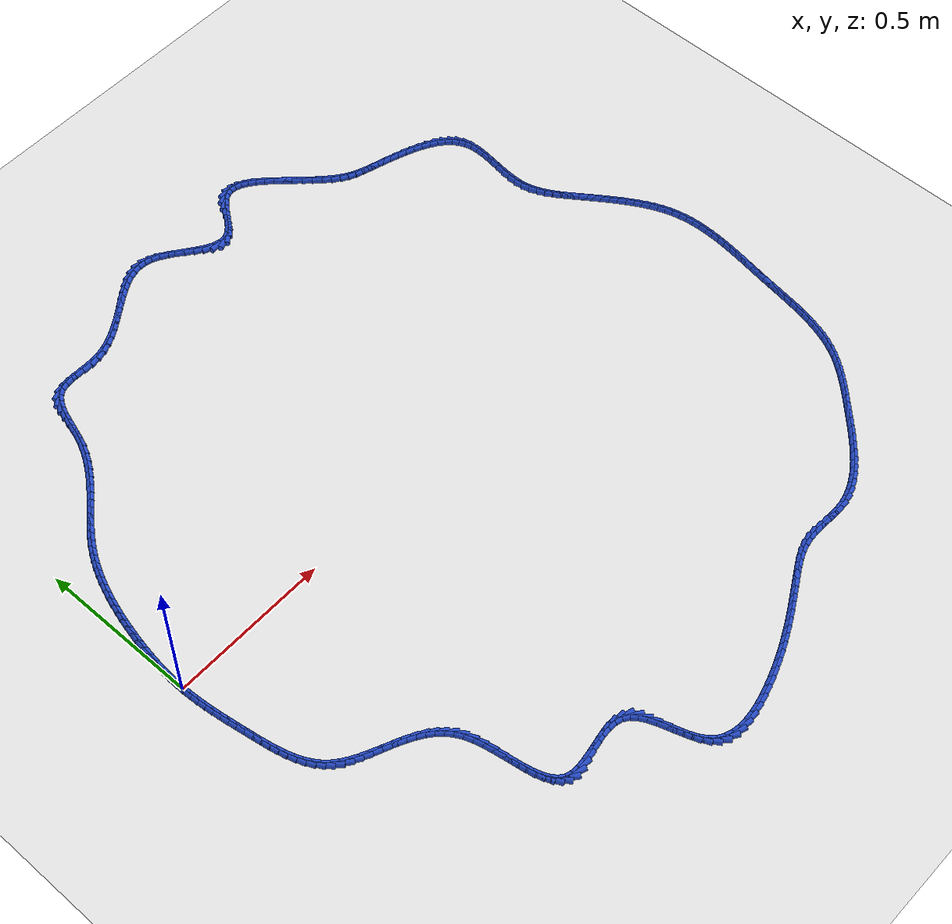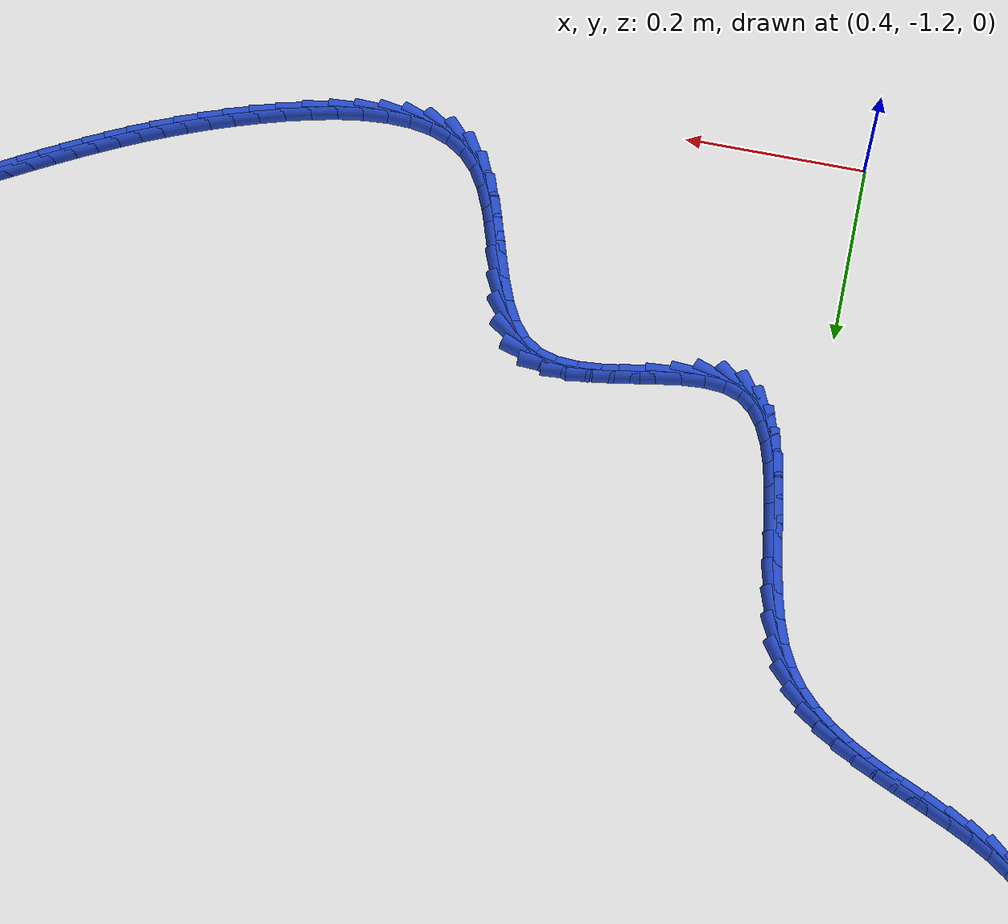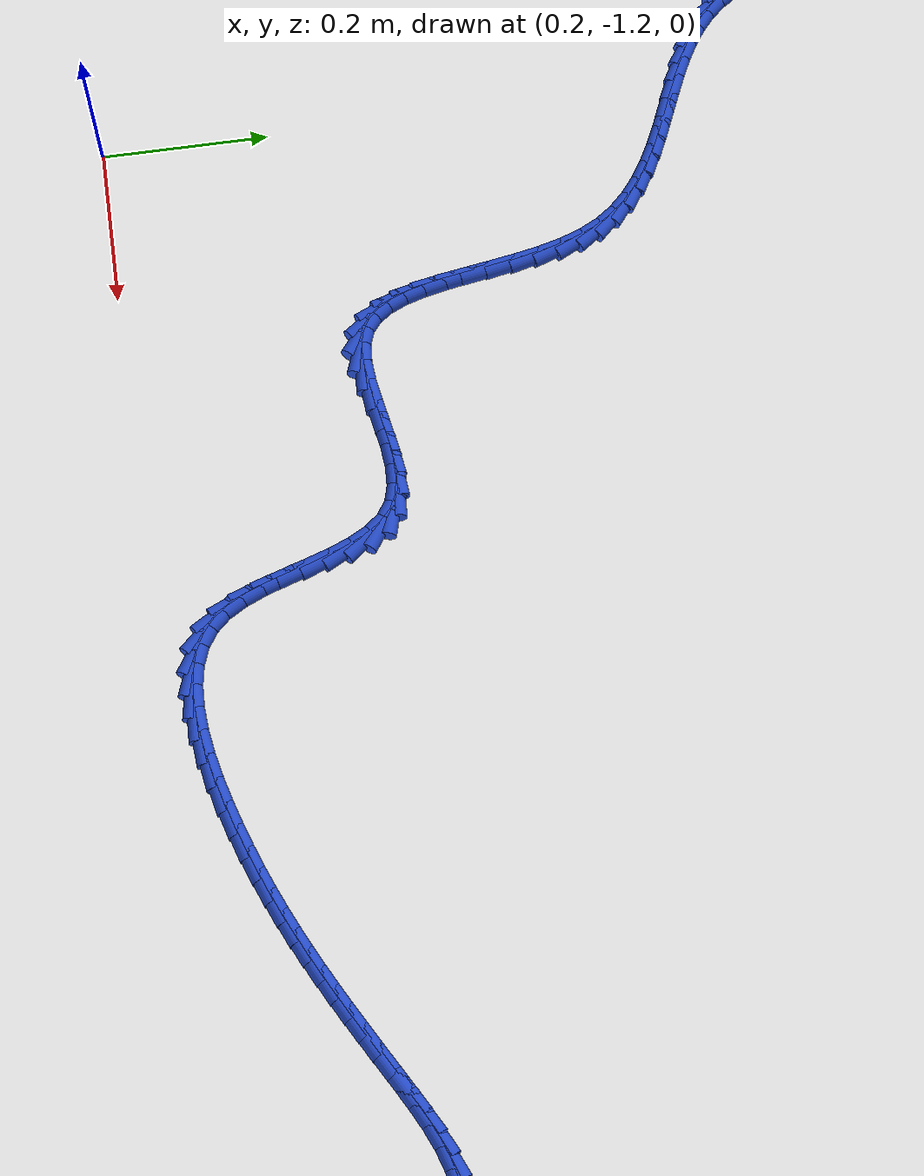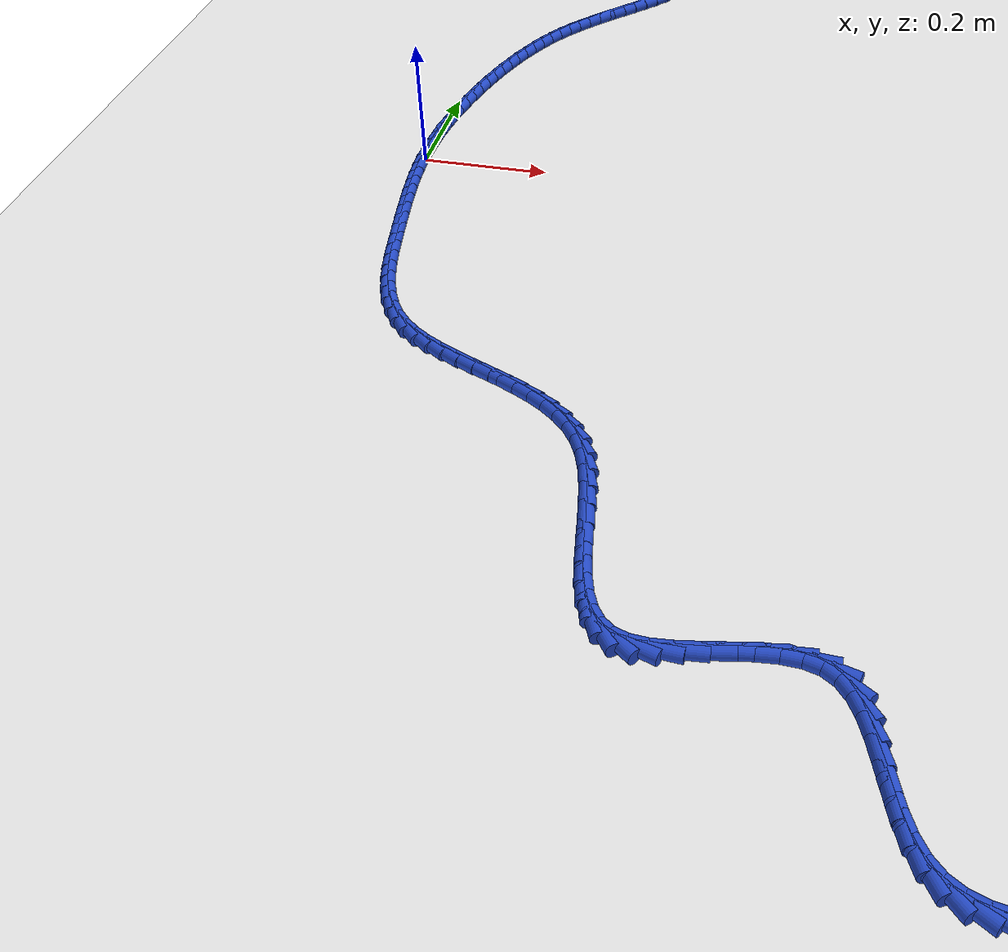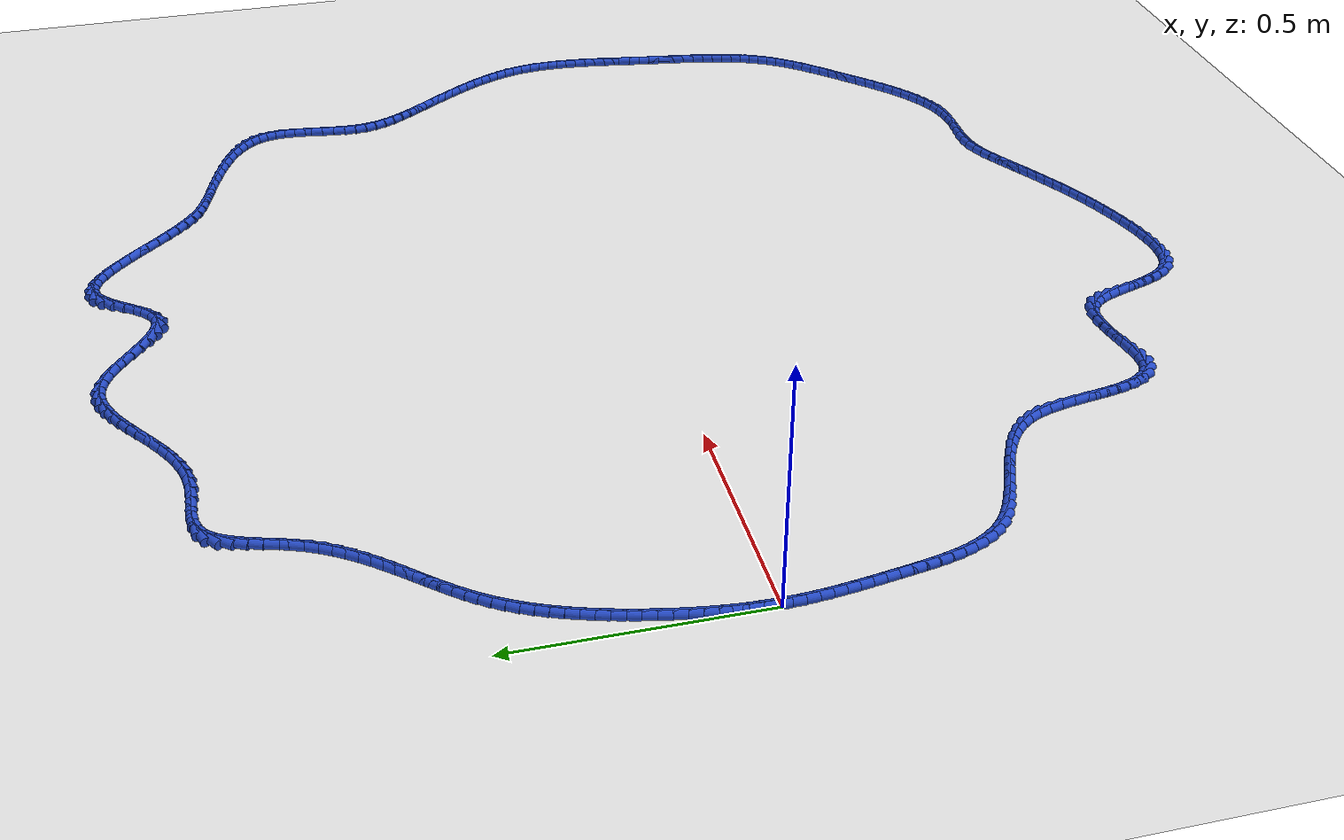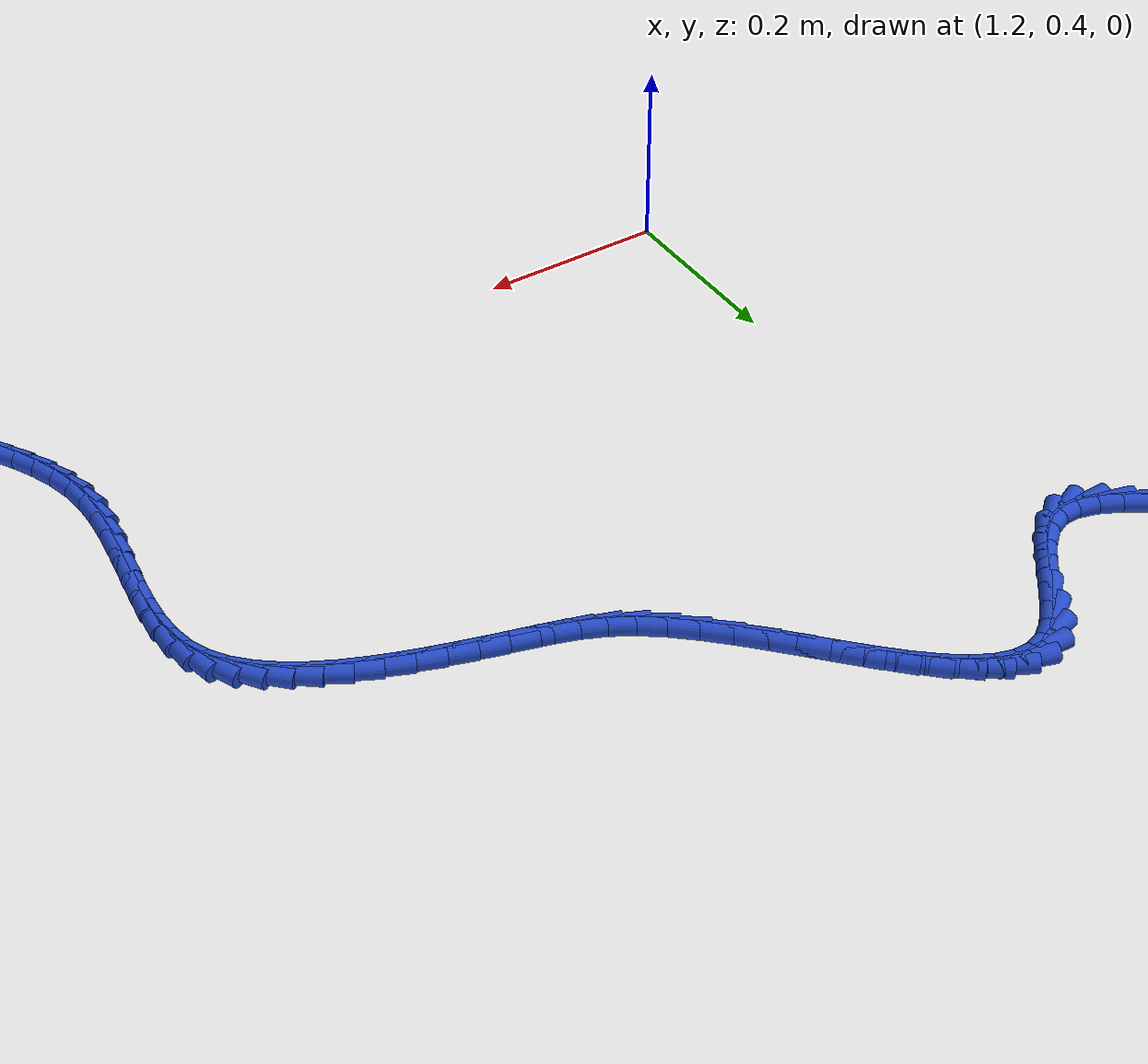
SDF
<sdf version="1.6">
 <world name="default">
  <light name="sun" type="directional">
   <pose>0 0 10 0 -0 0</pose>
   <diffuse>0.8 0.8 0.8 1</diffuse>
   <specular>0.2 0.2 0.2 1</specular>
   <attenuation>
    <range>1000</range>
    <constant>0.9</constant>
    <linear>0.01</linear>
    <quadratic>0.001</quadratic>
   </attenuation>
   <direction>-0.5 0.1 -0.9</direction>
  </light>
  <model name="ground_plane">
   <static>1</static>
   <link name="link">
    <collision name="collision">
     <geometry><plane><normal>0 0 1</normal><size>100 100</size></plane></geometry>
     <surface><friction><ode><mu>100</mu><mu2>50</mu2></ode></friction></surface>
    </collision>
    <visual name="visual">
     <cast_shadows>0</cast_shadows>
     <geometry><plane><normal>0 0 1</normal><size>100 100</size></plane></geometry>
     <material>
      <script><uri>file://media/materials/scripts/gazebo.material</uri><name>Gazebo/WhiteGlow</name></script>
     </material>
    </visual>
   </link>
  </model>
  <gravity>0 0 -9.8</gravity>
  <magnetic_field>6e-06 2.3e-05 -4.2e-05</magnetic_field>
  <atmosphere type="adiabatic"/>
  <physics name="default_physics" default="0" type="ode">
   <max_step_size>0.001</max_step_size>
   <real_time_factor>1</real_time_factor>
   <real_time_update_rate>1000</real_time_update_rate>
  </physics>
  <scene><ambient>0.4 0.4 0.4 1</ambient><background>0.7 0.7 0.7 1</background><shadows>1</shadows></scene>
  <spherical_coordinates>
   <surface_model>EARTH_WGS84</surface_model>
   <latitude_deg>0</latitude_deg>
   <longitude_deg>0</longitude_deg>
   <elevation>0</elevation>
   <heading_deg>0</heading_deg>
  </spherical_coordinates>
  <model name="line">
   <link name="link_0">
    <pose>3.0357660829594124e-18 -5.551115123125783e-17 0.01 0 1.57 1.5662700191625272</pose>
    <collision name="collision">
     <geometry><cylinder><radius>0.01</radius><length>0.08</length></cylinder></geometry>
    </collision>
    <visual name="visual">
     <material>
      <script><name>Gazebo/Blue</name><uri>file://media/materials/scripts/gazebo.material</uri></script>
     </material>
     <geometry><cylinder><radius>0.01</radius><length>0.08</length></cylinder></geometry>
    </visual>
   </link>
   <link name="link_1">
    <pose>0.00011356239113108886 0.025089239357680544 0.01 0 1.57 1.5347855059834898</pose>
    <collision name="collision">
     <geometry><cylinder><radius>0.01</radius><length>0.08</length></cylinder></geometry>
    </collision>
    <visual name="visual">
     <material>
      <script><name>Gazebo/Blue</name><uri>file://media/materials/scripts/gazebo.material</uri></script>
     </material>
     <geometry><cylinder><radius>0.01</radius><length>0.08</length></cylinder></geometry>
    </visual>
   </link>
   <link name="link_2">
    <pose>0.0010207351785241198 0.050270021100066814 0.01 0 1.57 1.5051376449260008</pose>
    <collision name="collision">
     <geometry><cylinder><radius>0.01</radius><length>0.08</length></cylinder></geometry>
    </collision>
    <visual name="visual">
     <material>
      <script><name>Gazebo/Blue</name><uri>file://media/materials/scripts/gazebo.material</uri></script>
     </material>
     <geometry><cylinder><radius>0.01</radius><length>0.08</length></cylinder></geometry>
    </visual>
   </link>
   <link name="link_3">
    <pose>0.002681473748511457 0.07552717401087107 0.01 0 1.57 1.477293541972339</pose>
    <collision name="collision">
     <geometry><cylinder><radius>0.01</radius><length>0.08</length></cylinder></geometry>
    </collision>
    <visual name="visual">
     <material>
      <script><name>Gazebo/Blue</name><uri>file://media/materials/scripts/gazebo.material</uri></script>
     </material>
     <geometry><cylinder><radius>0.01</radius><length>0.08</length></cylinder></geometry>
    </visual>
   </link>
   <link name="link_4">
    <pose>0.0050557334874254635 0.10084552687380567 0.01 0 1.57 1.4512115327179123</pose>
    <collision name="collision">
     <geometry><cylinder><radius>0.01</radius><length>0.08</length></cylinder></geometry>
    </collision>
    <visual name="visual">
     <material>
      <script><name>Gazebo/Blue</name><uri>file://media/materials/scripts/gazebo.material</uri></script>
     </material>
     <geometry><cylinder><radius>0.01</radius><length>0.08</length></cylinder></geometry>
    </visual>
   </link>
   <link name="link_5">
    <pose>0.008103469781598503 0.12620990847258295 0.01 0 1.57 1.4268439266841488</pose>
    <collision name="collision">
     <geometry><cylinder><radius>0.01</radius><length>0.08</length></cylinder></geometry>
    </collision>
    <visual name="visual">
     <material>
      <script><name>Gazebo/Blue</name><uri>file://media/materials/scripts/gazebo.material</uri></script>
     </material>
     <geometry><cylinder><radius>0.01</radius><length>0.08</length></cylinder></geometry>
    </visual>
   </link>
   <link name="link_6">
    <pose>0.011784638017362948 0.15160514759091534 0.01 0 1.57 1.404139370585922</pose>
    <collision name="collision">
     <geometry><cylinder><radius>0.01</radius><length>0.08</length></cylinder></geometry>
    </collision>
    <visual name="visual">
     <material>
      <script><name>Gazebo/Blue</name><uri>file://media/materials/scripts/gazebo.material</uri></script>
     </material>
     <geometry><cylinder><radius>0.01</radius><length>0.08</length></cylinder></geometry>
    </visual>
   </link>
   <link name="link_7">
    <pose>0.016059193581051148 0.17701607301251507 0.01 0 1.57 1.3830448410429423</pose>
    <collision name="collision">
     <geometry><cylinder><radius>0.01</radius><length>0.08</length></cylinder></geometry>
    </collision>
    <visual name="visual">
     <material>
      <script><name>Gazebo/Blue</name><uri>file://media/materials/scripts/gazebo.material</uri></script>
     </material>
     <geometry><cylinder><radius>0.01</radius><length>0.08</length></cylinder></geometry>
    </visual>
   </link>
   <link name="link_8">
    <pose>0.020887091858995475 0.2024275135210945 0.01 0 1.57 1.363501683285036</pose>
    <collision name="collision">
     <geometry><cylinder><radius>0.01</radius><length>0.08</length></cylinder></geometry>
    </collision>
    <visual name="visual">
     <material>
      <script><name>Gazebo/Blue</name><uri>file://media/materials/scripts/gazebo.material</uri></script>
     </material>
     <geometry><cylinder><radius>0.01</radius><length>0.08</length></cylinder></geometry>
    </visual>
   </link>
   <link name="link_9">
    <pose>0.026228419726229763 0.22782421543325912 0.01 0 1.57 1.3443885876318216</pose>
    <collision name="collision">
     <geometry><cylinder><radius>0.01</radius><length>0.08</length></cylinder></geometry>
    </collision>
    <visual name="visual">
     <material>
      <script><name>Gazebo/Blue</name><uri>file://media/materials/scripts/gazebo.material</uri></script>
     </material>
     <geometry><cylinder><radius>0.01</radius><length>0.08</length></cylinder></geometry>
    </visual>
   </link>
   <link name="link_10">
    <pose>0.03206822150596183 0.2531752722488874 0.01 0 1.57 1.3233013821437325</pose>
    <collision name="collision">
     <geometry><cylinder><radius>0.01</radius><length>0.08</length></cylinder></geometry>
    </collision>
    <visual name="visual">
     <material>
      <script><name>Gazebo/Blue</name><uri>file://media/materials/scripts/gazebo.material</uri></script>
     </material>
     <geometry><cylinder><radius>0.01</radius><length>0.08</length></cylinder></geometry>
    </visual>
   </link>
   <link name="link_11">
    <pose>0.03844585578112786 0.27841571264090675 0.01 0 1.57 1.2998216217959722</pose>
    <collision name="collision">
     <geometry><cylinder><radius>0.01</radius><length>0.08</length></cylinder></geometry>
    </collision>
    <visual name="visual">
     <material>
      <script><name>Gazebo/Blue</name><uri>file://media/materials/scripts/gazebo.material</uri></script>
     </material>
     <geometry><cylinder><radius>0.01</radius><length>0.08</length></cylinder></geometry>
    </visual>
   </link>
   <link name="link_12">
    <pose>0.04540782260110202 0.30347608629606987 0.01 0 1.57 1.2738191148276392</pose>
    <collision name="collision">
     <geometry><cylinder><radius>0.01</radius><length>0.08</length></cylinder></geometry>
    </collision>
    <visual name="visual">
     <material>
      <script><name>Gazebo/Blue</name><uri>file://media/materials/scripts/gazebo.material</uri></script>
     </material>
     <geometry><cylinder><radius>0.01</radius><length>0.08</length></cylinder></geometry>
    </visual>
   </link>
   <link name="link_13">
    <pose>0.05300062201525856 0.3282869429011298 0.01 0 1.57 1.2451494826743204</pose>
    <collision name="collision">
     <geometry><cylinder><radius>0.01</radius><length>0.08</length></cylinder></geometry>
    </collision>
    <visual name="visual">
     <material>
      <script><name>Gazebo/Blue</name><uri>file://media/materials/scripts/gazebo.material</uri></script>
     </material>
     <geometry><cylinder><radius>0.01</radius><length>0.08</length></cylinder></geometry>
    </visual>
   </link>
   <link name="link_14">
    <pose>0.06127075407297165 0.3527788321428397 0.01 0 1.57 1.2136575063745054</pose>
    <collision name="collision">
     <geometry><cylinder><radius>0.01</radius><length>0.08</length></cylinder></geometry>
    </collision>
    <visual name="visual">
     <material>
      <script><name>Gazebo/Blue</name><uri>file://media/materials/scripts/gazebo.material</uri></script>
     </material>
     <geometry><cylinder><radius>0.01</radius><length>0.08</length></cylinder></geometry>
    </visual>
   </link>
   <link name="link_15">
    <pose>0.07026471882361549 0.3768823037079522 0.01 0 1.57 1.179181826876187</pose>
    <collision name="collision">
     <geometry><cylinder><radius>0.01</radius><length>0.08</length></cylinder></geometry>
    </collision>
    <visual name="visual">
     <material>
      <script><name>Gazebo/Blue</name><uri>file://media/materials/scripts/gazebo.material</uri></script>
     </material>
     <geometry><cylinder><radius>0.01</radius><length>0.08</length></cylinder></geometry>
    </visual>
   </link>
   <link name="link_16">
    <pose>0.08002901631656432 0.4005279072832208 0.01 0 1.57 1.1415614532896643</pose>
    <collision name="collision">
     <geometry><cylinder><radius>0.01</radius><length>0.08</length></cylinder></geometry>
    </collision>
    <visual name="visual">
     <material>
      <script><name>Gazebo/Blue</name><uri>file://media/materials/scripts/gazebo.material</uri></script>
     </material>
     <geometry><cylinder><radius>0.01</radius><length>0.08</length></cylinder></geometry>
    </visual>
   </link>
   <link name="link_17">
    <pose>0.0906101466011923 0.42364619255539804 0.01 0 1.57 1.1006445454075553</pose>
    <collision name="collision">
     <geometry><cylinder><radius>0.01</radius><length>0.08</length></cylinder></geometry>
    </collision>
    <visual name="visual">
     <material>
      <script><name>Gazebo/Blue</name><uri>file://media/materials/scripts/gazebo.material</uri></script>
     </material>
     <geometry><cylinder><radius>0.01</radius><length>0.08</length></cylinder></geometry>
    </visual>
   </link>
   <link name="link_18">
    <pose>0.10205460972687364 0.4461677092112369 0.01 0 1.57 1.0562998773934744</pose>
    <collision name="collision">
     <geometry><cylinder><radius>0.01</radius><length>0.08</length></cylinder></geometry>
    </collision>
    <visual name="visual">
     <material>
      <script><name>Gazebo/Blue</name><uri>file://media/materials/scripts/gazebo.material</uri></script>
     </material>
     <geometry><cylinder><radius>0.01</radius><length>0.08</length></cylinder></geometry>
    </visual>
   </link>
   <link name="link_19">
    <pose>0.11440890574298257 0.4680230069374907 0.01 0 1.57 1.0084312079287099</pose>
    <collision name="collision">
     <geometry><cylinder><radius>0.01</radius><length>0.08</length></cylinder></geometry>
    </collision>
    <visual name="visual">
     <material>
      <script><name>Gazebo/Blue</name><uri>file://media/materials/scripts/gazebo.material</uri></script>
     </material>
     <geometry><cylinder><radius>0.01</radius><length>0.08</length></cylinder></geometry>
    </visual>
   </link>
   <link name="link_20">
    <pose>0.12771953469889322 0.489142635420912 0.01 0 1.57 0.9582909669125129</pose>
    <collision name="collision">
     <geometry><cylinder><radius>0.01</radius><length>0.08</length></cylinder></geometry>
    </collision>
    <visual name="visual">
     <material>
      <script><name>Gazebo/Blue</name><uri>file://media/materials/scripts/gazebo.material</uri></script>
     </material>
     <geometry><cylinder><radius>0.01</radius><length>0.08</length></cylinder></geometry>
    </visual>
   </link>
   <link name="link_21">
    <pose>0.14201038994826592 0.5094810137284753 0.01 0 1.57 0.9143157773765004</pose>
    <collision name="collision">
     <geometry><cylinder><radius>0.01</radius><length>0.08</length></cylinder></geometry>
    </collision>
    <visual name="visual">
     <material>
      <script><name>Gazebo/Blue</name><uri>file://media/materials/scripts/gazebo.material</uri></script>
     </material>
     <geometry><cylinder><radius>0.01</radius><length>0.08</length></cylinder></geometry>
    </visual>
   </link>
   <link name="link_22">
    <pose>0.15716105924483434 0.5291449266366892 0.01 0 1.57 0.8800797077235053</pose>
    <collision name="collision">
     <geometry><cylinder><radius>0.01</radius><length>0.08</length></cylinder></geometry>
    </collision>
    <visual name="visual">
     <material>
      <script><name>Gazebo/Blue</name><uri>file://media/materials/scripts/gazebo.material</uri></script>
     </material>
     <geometry><cylinder><radius>0.01</radius><length>0.08</length></cylinder></geometry>
    </visual>
   </link>
   <link name="link_23">
    <pose>0.17299439910585873 0.5483010588504262 0.01 0 1.57 0.855727843662233</pose>
    <collision name="collision">
     <geometry><cylinder><radius>0.01</radius><length>0.08</length></cylinder></geometry>
    </collision>
    <visual name="visual">
     <material>
      <script><name>Gazebo/Blue</name><uri>file://media/materials/scripts/gazebo.material</uri></script>
     </material>
     <geometry><cylinder><radius>0.01</radius><length>0.08</length></cylinder></geometry>
    </visual>
   </link>
   <link name="link_24">
    <pose>0.18933313061972137 0.5671162380677419 0.01 0 1.57 0.8412541116425264</pose>
    <collision name="collision">
     <geometry><cylinder><radius>0.01</radius><length>0.08</length></cylinder></geometry>
    </collision>
    <visual name="visual">
     <material>
      <script><name>Gazebo/Blue</name><uri>file://media/materials/scripts/gazebo.material</uri></script>
     </material>
     <geometry><cylinder><radius>0.01</radius><length>0.08</length></cylinder></geometry>
    </visual>
   </link>
   <link name="link_25">
    <pose>0.20599997487480448 0.5857572919866918 0.01 0 1.57 0.83658063768396</pose>
    <collision name="collision">
     <geometry><cylinder><radius>0.01</radius><length>0.08</length></cylinder></geometry>
    </collision>
    <visual name="visual">
     <material>
      <script><name>Gazebo/Blue</name><uri>file://media/materials/scripts/gazebo.material</uri></script>
     </material>
     <geometry><cylinder><radius>0.01</radius><length>0.08</length></cylinder></geometry>
    </visual>
   </link>
   <link name="link_26">
    <pose>0.22281765295949033 0.6043910483053317 0.01 0 1.57 0.8416008328042557</pose>
    <collision name="collision">
     <geometry><cylinder><radius>0.01</radius><length>0.08</length></cylinder></geometry>
    </collision>
    <visual name="visual">
     <material>
      <script><name>Gazebo/Blue</name><uri>file://media/materials/scripts/gazebo.material</uri></script>
     </material>
     <geometry><cylinder><radius>0.01</radius><length>0.08</length></cylinder></geometry>
    </visual>
   </link>
   <link name="link_27">
    <pose>0.23960888596216107 0.623184334721717 0.01 0 1.57 0.8561935982739316</pose>
    <collision name="collision">
     <geometry><cylinder><radius>0.01</radius><length>0.08</length></cylinder></geometry>
    </collision>
    <visual name="visual">
     <material>
      <script><name>Gazebo/Blue</name><uri>file://media/materials/scripts/gazebo.material</uri></script>
     </material>
     <geometry><cylinder><radius>0.01</radius><length>0.08</length></cylinder></geometry>
    </visual>
   </link>
   <link name="link_28">
    <pose>0.256196394971199 0.6423039789339033 0.01 0 1.57 0.8802103791430471</pose>
    <collision name="collision">
     <geometry><cylinder><radius>0.01</radius><length>0.08</length></cylinder></geometry>
    </collision>
    <visual name="visual">
     <material>
      <script><name>Gazebo/Blue</name><uri>file://media/materials/scripts/gazebo.material</uri></script>
     </material>
     <geometry><cylinder><radius>0.01</radius><length>0.08</length></cylinder></geometry>
    </visual>
   </link>
   <link name="link_29">
    <pose>0.27240290107498655 0.6619168086399465 0.01 0 1.57 0.9134377540114774</pose>
    <collision name="collision">
     <geometry><cylinder><radius>0.01</radius><length>0.08</length></cylinder></geometry>
    </collision>
    <visual name="visual">
     <material>
      <script><name>Gazebo/Blue</name><uri>file://media/materials/scripts/gazebo.material</uri></script>
     </material>
     <geometry><cylinder><radius>0.01</radius><length>0.08</length></cylinder></geometry>
    </visual>
   </link>
   <link name="link_30">
    <pose>0.28805112536190564 0.6821896515379018 0.01 0 1.57 0.9555399088143963</pose>
    <collision name="collision">
     <geometry><cylinder><radius>0.01</radius><length>0.08</length></cylinder></geometry>
    </collision>
    <visual name="visual">
     <material>
      <script><name>Gazebo/Blue</name><uri>file://media/materials/scripts/gazebo.material</uri></script>
     </material>
     <geometry><cylinder><radius>0.01</radius><length>0.08</length></cylinder></geometry>
    </visual>
   </link>
   <link name="link_31">
    <pose>0.3029637889203389 0.7032893353258255 0.01 0 1.57 1.005988966866133</pose>
    <collision name="collision">
     <geometry><cylinder><radius>0.01</radius><length>0.08</length></cylinder></geometry>
    </collision>
    <visual name="visual">
     <material>
      <script><name>Gazebo/Blue</name><uri>file://media/materials/scripts/gazebo.material</uri></script>
     </material>
     <geometry><cylinder><radius>0.01</radius><length>0.08</length></cylinder></geometry>
    </visual>
   </link>
   <link name="link_32">
    <pose>0.3169636128386682 0.7253826877017722 0.01 0 1.57 1.0639968913932731</pose>
    <collision name="collision">
     <geometry><cylinder><radius>0.01</radius><length>0.08</length></cylinder></geometry>
    </collision>
    <visual name="visual">
     <material>
      <script><name>Gazebo/Blue</name><uri>file://media/materials/scripts/gazebo.material</uri></script>
     </material>
     <geometry><cylinder><radius>0.01</radius><length>0.08</length></cylinder></geometry>
    </visual>
   </link>
   <link name="link_33">
    <pose>0.329873318205276 0.7486365363637981 0.01 0 1.57 1.1284688029731784</pose>
    <collision name="collision">
     <geometry><cylinder><radius>0.01</radius><length>0.08</length></cylinder></geometry>
    </collision>
    <visual name="visual">
     <material>
      <script><name>Gazebo/Blue</name><uri>file://media/materials/scripts/gazebo.material</uri></script>
     </material>
     <geometry><cylinder><radius>0.01</radius><length>0.08</length></cylinder></geometry>
    </visual>
   </link>
   <link name="link_34">
    <pose>0.3415156261085445 0.7732177090099589 0.01 0 1.57 1.197690654093386</pose>
    <collision name="collision">
     <geometry><cylinder><radius>0.01</radius><length>0.08</length></cylinder></geometry>
    </collision>
    <visual name="visual">
     <material>
      <script><name>Gazebo/Blue</name><uri>file://media/materials/scripts/gazebo.material</uri></script>
     </material>
     <geometry><cylinder><radius>0.01</radius><length>0.08</length></cylinder></geometry>
    </visual>
   </link>
   <link name="link_35">
    <pose>0.35171942012218216 0.7992850104737067 0.01 0 1.57 1.2533651907833483</pose>
    <collision name="collision">
     <geometry><cylinder><radius>0.01</radius><length>0.08</length></cylinder></geometry>
    </collision>
    <visual name="visual">
     <material>
      <script><name>Gazebo/Blue</name><uri>file://media/materials/scripts/gazebo.material</uri></script>
     </material>
     <geometry><cylinder><radius>0.01</radius><length>0.08</length></cylinder></geometry>
    </visual>
   </link>
   <link name="link_36">
    <pose>0.36067110237499256 0.826531796535264 0.01 0 1.57 1.2722899167853536</pose>
    <collision name="collision">
     <geometry><cylinder><radius>0.01</radius><length>0.08</length></cylinder></geometry>
    </collision>
    <visual name="visual">
     <material>
      <script><name>Gazebo/Blue</name><uri>file://media/materials/scripts/gazebo.material</uri></script>
     </material>
     <geometry><cylinder><radius>0.01</radius><length>0.08</length></cylinder></geometry>
    </visual>
   </link>
   <link name="link_37">
    <pose>0.3691043083008502 0.853938986598863 0.01 0 1.57 1.2536323393062092</pose>
    <collision name="collision">
     <geometry><cylinder><radius>0.01</radius><length>0.08</length></cylinder></geometry>
    </collision>
    <visual name="visual">
     <material>
      <script><name>Gazebo/Blue</name><uri>file://media/materials/scripts/gazebo.material</uri></script>
     </material>
     <geometry><cylinder><radius>0.01</radius><length>0.08</length></cylinder></geometry>
    </visual>
   </link>
   <link name="link_38">
    <pose>0.3777989475128677 0.8804272562782846 0.01 0 1.57 1.1924047636396597</pose>
    <collision name="collision">
     <geometry><cylinder><radius>0.01</radius><length>0.08</length></cylinder></geometry>
    </collision>
    <visual name="visual">
     <material>
      <script><name>Gazebo/Blue</name><uri>file://media/materials/scripts/gazebo.material</uri></script>
     </material>
     <geometry><cylinder><radius>0.01</radius><length>0.08</length></cylinder></geometry>
    </visual>
   </link>
   <link name="link_39">
    <pose>0.38753492962415753 0.9049172811873103 0.01 0 1.57 1.0758616461413353</pose>
    <collision name="collision">
     <geometry><cylinder><radius>0.01</radius><length>0.08</length></cylinder></geometry>
    </collision>
    <visual name="visual">
     <material>
      <script><name>Gazebo/Blue</name><uri>file://media/materials/scripts/gazebo.material</uri></script>
     </material>
     <geometry><cylinder><radius>0.01</radius><length>0.08</length></cylinder></geometry>
    </visual>
   </link>
   <link name="link_40">
    <pose>0.39909216424783245 0.9263297369397216 0.01 0 1.57 0.8836725762204143</pose>
    <collision name="collision">
     <geometry><cylinder><radius>0.01</radius><length>0.08</length></cylinder></geometry>
    </collision>
    <visual name="visual">
     <material>
      <script><name>Gazebo/Blue</name><uri>file://media/materials/scripts/gazebo.material</uri></script>
     </material>
     <geometry><cylinder><radius>0.01</radius><length>0.08</length></cylinder></geometry>
    </visual>
   </link>
   <link name="link_41">
    <pose>0.4132505609970051 0.9435852991492997 0.01 0 1.57 0.6012549065101921</pose>
    <collision name="collision">
     <geometry><cylinder><radius>0.01</radius><length>0.08</length></cylinder></geometry>
    </collision>
    <visual name="visual">
     <material>
      <script><name>Gazebo/Blue</name><uri>file://media/materials/scripts/gazebo.material</uri></script>
     </material>
     <geometry><cylinder><radius>0.01</radius><length>0.08</length></cylinder></geometry>
    </visual>
   </link>
   <link name="link_42">
    <pose>0.4307848259505046 0.9556134656059172 0.01 0 1.57 0.30317155262397594</pose>
    <collision name="collision">
     <geometry><cylinder><radius>0.01</radius><length>0.08</length></cylinder></geometry>
    </collision>
    <visual name="visual">
     <material>
      <script><name>Gazebo/Blue</name><uri>file://media/materials/scripts/gazebo.material</uri></script>
     </material>
     <geometry><cylinder><radius>0.01</radius><length>0.08</length></cylinder></geometry>
    </visual>
   </link>
   <link name="link_43">
    <pose>0.4519452901344115 0.9622327700510799 0.01 0 1.57 0.11035234905984537</pose>
    <collision name="collision">
     <geometry><cylinder><radius>0.01</radius><length>0.08</length></cylinder></geometry>
    </collision>
    <visual name="visual">
     <material>
      <script><name>Gazebo/Blue</name><uri>file://media/materials/scripts/gazebo.material</uri></script>
     </material>
     <geometry><cylinder><radius>0.01</radius><length>0.08</length></cylinder></geometry>
    </visual>
   </link>
   <link name="link_44">
    <pose>0.47601607744643054 0.9648998731153317 0.01 0 1.57 0.01330063873549448</pose>
    <collision name="collision">
     <geometry><cylinder><radius>0.01</radius><length>0.08</length></cylinder></geometry>
    </collision>
    <visual name="visual">
     <material>
      <script><name>Gazebo/Blue</name><uri>file://media/materials/scripts/gazebo.material</uri></script>
     </material>
     <geometry><cylinder><radius>0.01</radius><length>0.08</length></cylinder></geometry>
    </visual>
   </link>
   <link name="link_45">
    <pose>0.5021772558047813 0.9652478540178977 0.01 0 1.57 -0.012323177175495761</pose>
    <collision name="collision">
     <geometry><cylinder><radius>0.01</radius><length>0.08</length></cylinder></geometry>
    </collision>
    <visual name="visual">
     <material>
      <script><name>Gazebo/Blue</name><uri>file://media/materials/scripts/gazebo.material</uri></script>
     </material>
     <geometry><cylinder><radius>0.01</radius><length>0.08</length></cylinder></geometry>
    </visual>
   </link>
   <link name="link_46">
    <pose>0.5296088931276831 0.9649097919780015 0.01 0 1.57 0.021837524062655555</pose>
    <collision name="collision">
     <geometry><cylinder><radius>0.01</radius><length>0.08</length></cylinder></geometry>
    </collision>
    <visual name="visual">
     <material>
      <script><name>Gazebo/Blue</name><uri>file://media/materials/scripts/gazebo.material</uri></script>
     </material>
     <geometry><cylinder><radius>0.01</radius><length>0.08</length></cylinder></geometry>
    </visual>
   </link>
   <link name="link_47">
    <pose>0.5574910573333552 0.965518766214868 0.01 0 1.57 0.11528833036657696</pose>
    <collision name="collision">
     <geometry><cylinder><radius>0.01</radius><length>0.08</length></cylinder></geometry>
    </collision>
    <visual name="visual">
     <material>
      <script><name>Gazebo/Blue</name><uri>file://media/materials/scripts/gazebo.material</uri></script>
     </material>
     <geometry><cylinder><radius>0.01</radius><length>0.08</length></cylinder></geometry>
    </visual>
   </link>
   <link name="link_48">
    <pose>0.5850050132265947 0.9687049329804212 0.01 0 1.57 0.24897350602909968</pose>
    <collision name="collision">
     <geometry><cylinder><radius>0.01</radius><length>0.08</length></cylinder></geometry>
    </collision>
    <visual name="visual">
     <material>
      <script><name>Gazebo/Blue</name><uri>file://media/materials/scripts/gazebo.material</uri></script>
     </material>
     <geometry><cylinder><radius>0.01</radius><length>0.08</length></cylinder></geometry>
    </visual>
   </link>
   <link name="link_49">
    <pose>0.6115915964908748 0.9754645395123885 0.01 0 1.57 0.3681971482688158</pose>
    <collision name="collision">
     <geometry><cylinder><radius>0.01</radius><length>0.08</length></cylinder></geometry>
    </collision>
    <visual name="visual">
     <material>
      <script><name>Gazebo/Blue</name><uri>file://media/materials/scripts/gazebo.material</uri></script>
     </material>
     <geometry><cylinder><radius>0.01</radius><length>0.08</length></cylinder></geometry>
    </visual>
   </link>
   <link name="link_50">
    <pose>0.6372736697629611 0.9853724404251105 0.01 0 1.57 0.4635773042794441</pose>
    <collision name="collision">
     <geometry><cylinder><radius>0.01</radius><length>0.08</length></cylinder></geometry>
    </collision>
    <visual name="visual">
     <material>
      <script><name>Gazebo/Blue</name><uri>file://media/materials/scripts/gazebo.material</uri></script>
     </material>
     <geometry><cylinder><radius>0.01</radius><length>0.08</length></cylinder></geometry>
    </visual>
   </link>
   <link name="link_51">
    <pose>0.6621532975997116 0.9978100679762099 0.01 0 1.57 0.5355775466585364</pose>
    <collision name="collision">
     <geometry><cylinder><radius>0.01</radius><length>0.08</length></cylinder></geometry>
    </collision>
    <visual name="visual">
     <material>
      <script><name>Gazebo/Blue</name><uri>file://media/materials/scripts/gazebo.material</uri></script>
     </material>
     <geometry><cylinder><radius>0.01</radius><length>0.08</length></cylinder></geometry>
    </visual>
   </link>
   <link name="link_52">
    <pose>0.6863325445579858 1.0121588544233093 0.01 0 1.57 0.5856725200768663</pose>
    <collision name="collision">
     <geometry><cylinder><radius>0.01</radius><length>0.08</length></cylinder></geometry>
    </collision>
    <visual name="visual">
     <material>
      <script><name>Gazebo/Blue</name><uri>file://media/materials/scripts/gazebo.material</uri></script>
     </material>
     <geometry><cylinder><radius>0.01</radius><length>0.08</length></cylinder></geometry>
    </visual>
   </link>
   <link name="link_53">
    <pose>0.7099134751946414 1.0278002320240311 0.01 0 1.57 0.6152506030439742</pose>
    <collision name="collision">
     <geometry><cylinder><radius>0.01</radius><length>0.08</length></cylinder></geometry>
    </collision>
    <visual name="visual">
     <material>
      <script><name>Gazebo/Blue</name><uri>file://media/materials/scripts/gazebo.material</uri></script>
     </material>
     <geometry><cylinder><radius>0.01</radius><length>0.08</length></cylinder></geometry>
    </visual>
   </link>
   <link name="link_54">
    <pose>0.7329981540665376 1.0441156330359982 0.01 0 1.57 0.625000579297981</pose>
    <collision name="collision">
     <geometry><cylinder><radius>0.01</radius><length>0.08</length></cylinder></geometry>
    </collision>
    <visual name="visual">
     <material>
      <script><name>Gazebo/Blue</name><uri>file://media/materials/scripts/gazebo.material</uri></script>
     </material>
     <geometry><cylinder><radius>0.01</radius><length>0.08</length></cylinder></geometry>
    </visual>
   </link>
   <link name="link_55">
    <pose>0.7556886457305326 1.0604864897168333 0.01 0 1.57 0.6145774605897407</pose>
    <collision name="collision">
     <geometry><cylinder><radius>0.01</radius><length>0.08</length></cylinder></geometry>
    </collision>
    <visual name="visual">
     <material>
      <script><name>Gazebo/Blue</name><uri>file://media/materials/scripts/gazebo.material</uri></script>
     </material>
     <geometry><cylinder><radius>0.01</radius><length>0.08</length></cylinder></geometry>
    </visual>
   </link>
   <link name="link_56">
    <pose>0.7780870147434851 1.0762942343241588 0.01 0 1.57 0.5823868515626601</pose>
    <collision name="collision">
     <geometry><cylinder><radius>0.01</radius><length>0.08</length></cylinder></geometry>
    </collision>
    <visual name="visual">
     <material>
      <script><name>Gazebo/Blue</name><uri>file://media/materials/scripts/gazebo.material</uri></script>
     </material>
     <geometry><cylinder><radius>0.01</radius><length>0.08</length></cylinder></geometry>
    </visual>
   </link>
   <link name="link_57">
    <pose>0.8002953256622541 1.0909202991155982 0.01 0 1.57 0.5254495938514904</pose>
    <collision name="collision">
     <geometry><cylinder><radius>0.01</radius><length>0.08</length></cylinder></geometry>
    </collision>
    <visual name="visual">
     <material>
      <script><name>Gazebo/Blue</name><uri>file://media/materials/scripts/gazebo.material</uri></script>
     </material>
     <geometry><cylinder><radius>0.01</radius><length>0.08</length></cylinder></geometry>
    </visual>
   </link>
   <link name="link_58">
    <pose>0.8224156430436974 1.103746116348773 0.01 0 1.57 0.4395029515785107</pose>
    <collision name="collision">
     <geometry><cylinder><radius>0.01</radius><length>0.08</length></cylinder></geometry>
    </collision>
    <visual name="visual">
     <material>
      <script><name>Gazebo/Blue</name><uri>file://media/materials/scripts/gazebo.material</uri></script>
     </material>
     <geometry><cylinder><radius>0.01</radius><length>0.08</length></cylinder></geometry>
    </visual>
   </link>
   <link name="link_59">
    <pose>0.8445500314446743 1.1141531182813067 0.01 0 1.57 0.31983926378259636</pose>
    <collision name="collision">
     <geometry><cylinder><radius>0.01</radius><length>0.08</length></cylinder></geometry>
    </collision>
    <visual name="visual">
     <material>
      <script><name>Gazebo/Blue</name><uri>file://media/materials/scripts/gazebo.material</uri></script>
     </material>
     <geometry><cylinder><radius>0.01</radius><length>0.08</length></cylinder></geometry>
    </visual>
   </link>
   <link name="link_60">
    <pose>0.8668005554220428 1.1215227371708214 0.01 0 1.57 0.16380080513344852</pose>
    <collision name="collision">
     <geometry><cylinder><radius>0.01</radius><length>0.08</length></cylinder></geometry>
    </collision>
    <visual name="visual">
     <material>
      <script><name>Gazebo/Blue</name><uri>file://media/materials/scripts/gazebo.material</uri></script>
     </material>
     <geometry><cylinder><radius>0.01</radius><length>0.08</length></cylinder></geometry>
    </visual>
   </link>
   <link name="link_61">
    <pose>0.8892692795326624 1.1252364052749406 0.01 0 1.57 -0.024605621492440968</pose>
    <collision name="collision">
     <geometry><cylinder><radius>0.01</radius><length>0.08</length></cylinder></geometry>
    </collision>
    <visual name="visual">
     <material>
      <script><name>Gazebo/Blue</name><uri>file://media/materials/scripts/gazebo.material</uri></script>
     </material>
     <geometry><cylinder><radius>0.01</radius><length>0.08</length></cylinder></geometry>
    </visual>
   </link>
   <link name="link_62">
    <pose>0.9120582683333909 1.1246755548512861 0.01 0 1.57 -0.23077435446148625</pose>
    <collision name="collision">
     <geometry><cylinder><radius>0.01</radius><length>0.08</length></cylinder></geometry>
    </collision>
    <visual name="visual">
     <material>
      <script><name>Gazebo/Blue</name><uri>file://media/materials/scripts/gazebo.material</uri></script>
     </material>
     <geometry><cylinder><radius>0.01</radius><length>0.08</length></cylinder></geometry>
    </visual>
   </link>
   <link name="link_63">
    <pose>0.9352695578027016 1.119221822905175 0.01 0 1.57 -0.41806746413932455</pose>
    <collision name="collision">
     <geometry><cylinder><radius>0.01</radius><length>0.08</length></cylinder></geometry>
    </collision>
    <visual name="visual">
     <material>
      <script><name>Gazebo/Blue</name><uri>file://media/materials/scripts/gazebo.material</uri></script>
     </material>
     <geometry><cylinder><radius>0.01</radius><length>0.08</length></cylinder></geometry>
    </visual>
   </link>
   <link name="link_64">
    <pose>0.958942645639854 1.1087048972412237 0.01 0 1.57 -0.5393468073446842</pose>
    <collision name="collision">
     <geometry><cylinder><radius>0.01</radius><length>0.08</length></cylinder></geometry>
    </collision>
    <visual name="visual">
     <material>
      <script><name>Gazebo/Blue</name><uri>file://media/materials/scripts/gazebo.material</uri></script>
     </material>
     <geometry><cylinder><radius>0.01</radius><length>0.08</length></cylinder></geometry>
    </visual>
   </link>
   <link name="link_65">
    <pose>0.9829219231563014 1.094352290709821 0.01 0 1.57 -0.6058230697008173</pose>
    <collision name="collision">
     <geometry><cylinder><radius>0.01</radius><length>0.08</length></cylinder></geometry>
    </collision>
    <visual name="visual">
     <material>
      <script><name>Gazebo/Blue</name><uri>file://media/materials/scripts/gazebo.material</uri></script>
     </material>
     <geometry><cylinder><radius>0.01</radius><length>0.08</length></cylinder></geometry>
    </visual>
   </link>
   <link name="link_66">
    <pose>1.0070138398468274 1.0776633474541317 0.01 0 1.57 -0.6305207519428306</pose>
    <collision name="collision">
     <geometry><cylinder><radius>0.01</radius><length>0.08</length></cylinder></geometry>
    </collision>
    <visual name="visual">
     <material>
      <script><name>Gazebo/Blue</name><uri>file://media/materials/scripts/gazebo.material</uri></script>
     </material>
     <geometry><cylinder><radius>0.01</radius><length>0.08</length></cylinder></geometry>
    </visual>
   </link>
   <link name="link_67">
    <pose>1.0310248452062123 1.0601374116173181 0.01 0 1.57 -0.6177038045477371</pose>
    <collision name="collision">
     <geometry><cylinder><radius>0.01</radius><length>0.08</length></cylinder></geometry>
    </collision>
    <visual name="visual">
     <material>
      <script><name>Gazebo/Blue</name><uri>file://media/materials/scripts/gazebo.material</uri></script>
     </material>
     <geometry><cylinder><radius>0.01</radius><length>0.08</length></cylinder></geometry>
    </visual>
   </link>
   <link name="link_68">
    <pose>1.05476138872924 1.0432738273425448 0.01 0 1.57 -0.5634997766094578</pose>
    <collision name="collision">
     <geometry><cylinder><radius>0.01</radius><length>0.08</length></cylinder></geometry>
    </collision>
    <visual name="visual">
     <material>
      <script><name>Gazebo/Blue</name><uri>file://media/materials/scripts/gazebo.material</uri></script>
     </material>
     <geometry><cylinder><radius>0.01</radius><length>0.08</length></cylinder></geometry>
    </visual>
   </link>
   <link name="link_69">
    <pose>1.078029919910692 1.0285719387729746 0.01 0 1.57 -0.45431052551628215</pose>
    <collision name="collision">
     <geometry><cylinder><radius>0.01</radius><length>0.08</length></cylinder></geometry>
    </collision>
    <visual name="visual">
     <material>
      <script><name>Gazebo/Blue</name><uri>file://media/materials/scripts/gazebo.material</uri></script>
     </material>
     <geometry><cylinder><radius>0.01</radius><length>0.08</length></cylinder></geometry>
    </visual>
   </link>
   <link name="link_70">
    <pose>1.1006368882453512 1.0175310900517718 0.01 0 1.57 -0.26403162958950593</pose>
    <collision name="collision">
     <geometry><cylinder><radius>0.01</radius><length>0.08</length></cylinder></geometry>
    </collision>
    <visual name="visual">
     <material>
      <script><name>Gazebo/Blue</name><uri>file://media/materials/scripts/gazebo.material</uri></script>
     </material>
     <geometry><cylinder><radius>0.01</radius><length>0.08</length></cylinder></geometry>
    </visual>
   </link>
   <link name="link_71">
    <pose>1.122388743227999 1.0116506253220996 0.01 0 1.57 0.0376220122311731</pose>
    <collision name="collision">
     <geometry><cylinder><radius>0.01</radius><length>0.08</length></cylinder></geometry>
    </collision>
    <visual name="visual">
     <material>
      <script><name>Gazebo/Blue</name><uri>file://media/materials/scripts/gazebo.material</uri></script>
     </material>
     <geometry><cylinder><radius>0.01</radius><length>0.08</length></cylinder></geometry>
    </visual>
   </link>
   <link name="link_72">
    <pose>1.1430919343534187 1.0124298887271217 0.01 0 1.57 0.4241845442379834</pose>
    <collision name="collision">
     <geometry><cylinder><radius>0.01</radius><length>0.08</length></cylinder></geometry>
    </collision>
    <visual name="visual">
     <material>
      <script><name>Gazebo/Blue</name><uri>file://media/materials/scripts/gazebo.material</uri></script>
     </material>
     <geometry><cylinder><radius>0.01</radius><length>0.08</length></cylinder></geometry>
    </visual>
   </link>
   <link name="link_73">
    <pose>1.1625707542399282 1.0212265438096948 0.01 0 1.57 0.7154694932736173</pose>
    <collision name="collision">
     <geometry><cylinder><radius>0.01</radius><length>0.08</length></cylinder></geometry>
    </collision>
    <visual name="visual">
     <material>
      <script><name>Gazebo/Blue</name><uri>file://media/materials/scripts/gazebo.material</uri></script>
     </material>
     <geometry><cylinder><radius>0.01</radius><length>0.08</length></cylinder></geometry>
    </visual>
   </link>
   <link name="link_74">
    <pose>1.1809287151039338 1.0371811534916233 0.01 0 1.57 0.8623224712732442</pose>
    <collision name="collision">
     <geometry><cylinder><radius>0.01</radius><length>0.08</length></cylinder></geometry>
    </collision>
    <visual name="visual">
     <material>
      <script><name>Gazebo/Blue</name><uri>file://media/materials/scripts/gazebo.material</uri></script>
     </material>
     <geometry><cylinder><radius>0.01</radius><length>0.08</length></cylinder></geometry>
    </visual>
   </link>
   <link name="link_75">
    <pose>1.1984907068357686 1.0576764650481187 0.01 0 1.57 0.9182277332515708</pose>
    <collision name="collision">
     <geometry><cylinder><radius>0.01</radius><length>0.08</length></cylinder></geometry>
    </collision>
    <visual name="visual">
     <material>
      <script><name>Gazebo/Blue</name><uri>file://media/materials/scripts/gazebo.material</uri></script>
     </material>
     <geometry><cylinder><radius>0.01</radius><length>0.08</length></cylinder></geometry>
    </visual>
   </link>
   <link name="link_76">
    <pose>1.2155876983083787 1.0800469565203614 0.01 0 1.57 0.9046228854170388</pose>
    <collision name="collision">
     <geometry><cylinder><radius>0.01</radius><length>0.08</length></cylinder></geometry>
    </collision>
    <visual name="visual">
     <material>
      <script><name>Gazebo/Blue</name><uri>file://media/materials/scripts/gazebo.material</uri></script>
     </material>
     <geometry><cylinder><radius>0.01</radius><length>0.08</length></cylinder></geometry>
    </visual>
   </link>
   <link name="link_77">
    <pose>1.2325506583947103 1.101627105949532 0.01 0 1.57 0.812723376417342</pose>
    <collision name="collision">
     <geometry><cylinder><radius>0.01</radius><length>0.08</length></cylinder></geometry>
    </collision>
    <visual name="visual">
     <material>
      <script><name>Gazebo/Blue</name><uri>file://media/materials/scripts/gazebo.material</uri></script>
     </material>
     <geometry><cylinder><radius>0.01</radius><length>0.08</length></cylinder></geometry>
    </visual>
   </link>
   <link name="link_78">
    <pose>1.2497105559677097 1.11975139137681 0.01 0 1.57 0.6005722531968354</pose>
    <collision name="collision">
     <geometry><cylinder><radius>0.01</radius><length>0.08</length></cylinder></geometry>
    </collision>
    <visual name="visual">
     <material>
      <script><name>Gazebo/Blue</name><uri>file://media/materials/scripts/gazebo.material</uri></script>
     </material>
     <geometry><cylinder><radius>0.01</radius><length>0.08</length></cylinder></geometry>
    </visual>
   </link>
   <link name="link_79">
    <pose>1.26738684605833 1.1318592475972244 0.01 0 1.57 0.2818731334515106</pose>
    <collision name="collision">
     <geometry><cylinder><radius>0.01</radius><length>0.08</length></cylinder></geometry>
    </collision>
    <visual name="visual">
     <material>
      <script><name>Gazebo/Blue</name><uri>file://media/materials/scripts/gazebo.material</uri></script>
     </material>
     <geometry><cylinder><radius>0.01</radius><length>0.08</length></cylinder></geometry>
    </visual>
   </link>
   <link name="link_80">
    <pose>1.2857044179222725 1.1371637130555101 0.01 0 1.57 -0.04270730599006626</pose>
    <collision name="collision">
     <geometry><cylinder><radius>0.01</radius><length>0.08</length></cylinder></geometry>
    </collision>
    <visual name="visual">
     <material>
      <script><name>Gazebo/Blue</name><uri>file://media/materials/scripts/gazebo.material</uri></script>
     </material>
     <geometry><cylinder><radius>0.01</radius><length>0.08</length></cylinder></geometry>
    </visual>
   </link>
   <link name="link_81">
    <pose>1.3046260996672308 1.1363551273466683 0.01 0 1.57 -0.3074407791411573</pose>
    <collision name="collision">
     <geometry><cylinder><radius>0.01</radius><length>0.08</length></cylinder></geometry>
    </collision>
    <visual name="visual">
     <material>
      <script><name>Gazebo/Blue</name><uri>file://media/materials/scripts/gazebo.material</uri></script>
     </material>
     <geometry><cylinder><radius>0.01</radius><length>0.08</length></cylinder></geometry>
    </visual>
   </link>
   <link name="link_82">
    <pose>1.3241097746555475 1.1301689048913672 0.01 0 1.57 -0.49615941338677133</pose>
    <collision name="collision">
     <geometry><cylinder><radius>0.01</radius><length>0.08</length></cylinder></geometry>
    </collision>
    <visual name="visual">
     <material>
      <script><name>Gazebo/Blue</name><uri>file://media/materials/scripts/gazebo.material</uri></script>
     </material>
     <geometry><cylinder><radius>0.01</radius><length>0.08</length></cylinder></geometry>
    </visual>
   </link>
   <link name="link_83">
    <pose>1.3441133262495661 1.1193404601102779 0.01 0 1.57 -0.6236598691198544</pose>
    <collision name="collision">
     <geometry><cylinder><radius>0.01</radius><length>0.08</length></cylinder></geometry>
    </collision>
    <visual name="visual">
     <material>
      <script><name>Gazebo/Blue</name><uri>file://media/materials/scripts/gazebo.material</uri></script>
     </material>
     <geometry><cylinder><radius>0.01</radius><length>0.08</length></cylinder></geometry>
    </visual>
   </link>
   <link name="link_84">
    <pose>1.3645946378116283 1.1046052074240673 0.01 0 1.57 -0.7080148838807767</pose>
    <collision name="collision">
     <geometry><cylinder><radius>0.01</radius><length>0.08</length></cylinder></geometry>
    </collision>
    <visual name="visual">
     <material>
      <script><name>Gazebo/Blue</name><uri>file://media/materials/scripts/gazebo.material</uri></script>
     </material>
     <geometry><cylinder><radius>0.01</radius><length>0.08</length></cylinder></geometry>
    </visual>
   </link>
   <link name="link_85">
    <pose>1.3855115927040782 1.0866985612534064 0.01 0 1.57 -0.762166229607625</pose>
    <collision name="collision">
     <geometry><cylinder><radius>0.01</radius><length>0.08</length></cylinder></geometry>
    </collision>
    <visual name="visual">
     <material>
      <script><name>Gazebo/Blue</name><uri>file://media/materials/scripts/gazebo.material</uri></script>
     </material>
     <geometry><cylinder><radius>0.01</radius><length>0.08</length></cylinder></geometry>
    </visual>
   </link>
   <link name="link_86">
    <pose>1.4068220742892577 1.0663559360189627 0.01 0 1.57 -0.7941222876967864</pose>
    <collision name="collision">
     <geometry><cylinder><radius>0.01</radius><length>0.08</length></cylinder></geometry>
    </collision>
    <visual name="visual">
     <material>
      <script><name>Gazebo/Blue</name><uri>file://media/materials/scripts/gazebo.material</uri></script>
     </material>
     <geometry><cylinder><radius>0.01</radius><length>0.08</length></cylinder></geometry>
    </visual>
   </link>
   <link name="link_87">
    <pose>1.428483965929511 1.0443127461414061 0.01 0 1.57 -0.80845245938409</pose>
    <collision name="collision">
     <geometry><cylinder><radius>0.01</radius><length>0.08</length></cylinder></geometry>
    </collision>
    <visual name="visual">
     <material>
      <script><name>Gazebo/Blue</name><uri>file://media/materials/scripts/gazebo.material</uri></script>
     </material>
     <geometry><cylinder><radius>0.01</radius><length>0.08</length></cylinder></geometry>
    </visual>
   </link>
   <link name="link_88">
    <pose>1.45045515098718 1.021304406041406 0.01 0 1.57 -0.8073777449323576</pose>
    <collision name="collision">
     <geometry><cylinder><radius>0.01</radius><length>0.08</length></cylinder></geometry>
    </collision>
    <visual name="visual">
     <material>
      <script><name>Gazebo/Blue</name><uri>file://media/materials/scripts/gazebo.material</uri></script>
     </material>
     <geometry><cylinder><radius>0.01</radius><length>0.08</length></cylinder></geometry>
    </visual>
   </link>
   <link name="link_89">
    <pose>1.4726935128246075 0.9980663301396312 0.01 0 1.57 -0.7913494246480318</pose>
    <collision name="collision">
     <geometry><cylinder><radius>0.01</radius><length>0.08</length></cylinder></geometry>
    </collision>
    <visual name="visual">
     <material>
      <script><name>Gazebo/Blue</name><uri>file://media/materials/scripts/gazebo.material</uri></script>
     </material>
     <geometry><cylinder><radius>0.01</radius><length>0.08</length></cylinder></geometry>
    </visual>
   </link>
   <link name="link_90">
    <pose>1.495156934804137 0.975333932856751 0.01 0 1.57 -0.7592346237853783</pose>
    <collision name="collision">
     <geometry><cylinder><radius>0.01</radius><length>0.08</length></cylinder></geometry>
    </collision>
    <visual name="visual">
     <material>
      <script><name>Gazebo/Blue</name><uri>file://media/materials/scripts/gazebo.material</uri></script>
     </material>
     <geometry><cylinder><radius>0.01</radius><length>0.08</length></cylinder></geometry>
    </visual>
   </link>
   <link name="link_91">
    <pose>1.5178033002881106 0.9538426286134337 0.01 0 1.57 -0.708193961958227</pose>
    <collision name="collision">
     <geometry><cylinder><radius>0.01</radius><length>0.08</length></cylinder></geometry>
    </collision>
    <visual name="visual">
     <material>
      <script><name>Gazebo/Blue</name><uri>file://media/materials/scripts/gazebo.material</uri></script>
     </material>
     <geometry><cylinder><radius>0.01</radius><length>0.08</length></cylinder></geometry>
    </visual>
   </link>
   <link name="link_92">
    <pose>1.5405904926388718 0.9343278318303494 0.01 0 1.57 -0.6333134699912337</pose>
    <collision name="collision">
     <geometry><cylinder><radius>0.01</radius><length>0.08</length></cylinder></geometry>
    </collision>
    <visual name="visual">
     <material>
      <script><name>Gazebo/Blue</name><uri>file://media/materials/scripts/gazebo.material</uri></script>
     </material>
     <geometry><cylinder><radius>0.01</radius><length>0.08</length></cylinder></geometry>
    </visual>
   </link>
   <link name="link_93">
    <pose>1.5634763952187631 0.9175249569281672 0.01 0 1.57 -0.5283515220598164</pose>
    <collision name="collision">
     <geometry><cylinder><radius>0.01</radius><length>0.08</length></cylinder></geometry>
    </collision>
    <visual name="visual">
     <material>
      <script><name>Gazebo/Blue</name><uri>file://media/materials/scripts/gazebo.material</uri></script>
     </material>
     <geometry><cylinder><radius>0.01</radius><length>0.08</length></cylinder></geometry>
    </visual>
   </link>
   <link name="link_94">
    <pose>1.5864279836241901 0.904128005778663 0.01 0 1.57 -0.4151997910029941</pose>
    <collision name="collision">
     <geometry><cylinder><radius>0.01</radius><length>0.08</length></cylinder></geometry>
    </collision>
    <visual name="visual">
     <material>
      <script><name>Gazebo/Blue</name><uri>file://media/materials/scripts/gazebo.material</uri></script>
     </material>
     <geometry><cylinder><radius>0.01</radius><length>0.08</length></cylinder></geometry>
    </visual>
   </link>
   <link name="link_95">
    <pose>1.609615218904772 0.8939064390518999 0.01 0 1.57 -0.3313717219436235</pose>
    <collision name="collision">
     <geometry><cylinder><radius>0.01</radius><length>0.08</length></cylinder></geometry>
    </collision>
    <visual name="visual">
     <material>
      <script><name>Gazebo/Blue</name><uri>file://media/materials/scripts/gazebo.material</uri></script>
     </material>
     <geometry><cylinder><radius>0.01</radius><length>0.08</length></cylinder></geometry>
    </visual>
   </link>
   <link name="link_96">
    <pose>1.6334076961231012 0.8857204410765483 0.01 0 1.57 -0.2875968599010426</pose>
    <collision name="collision">
     <geometry><cylinder><radius>0.01</radius><length>0.08</length></cylinder></geometry>
    </collision>
    <visual name="visual">
     <material>
      <script><name>Gazebo/Blue</name><uri>file://media/materials/scripts/gazebo.material</uri></script>
     </material>
     <geometry><cylinder><radius>0.01</radius><length>0.08</length></cylinder></geometry>
    </visual>
   </link>
   <link name="link_97">
    <pose>1.6581834289297088 0.878391840834631 0.01 0 1.57 -0.27969026245600886</pose>
    <collision name="collision">
     <geometry><cylinder><radius>0.01</radius><length>0.08</length></cylinder></geometry>
    </collision>
    <visual name="visual">
     <material>
      <script><name>Gazebo/Blue</name><uri>file://media/materials/scripts/gazebo.material</uri></script>
     </material>
     <geometry><cylinder><radius>0.01</radius><length>0.08</length></cylinder></geometry>
    </visual>
   </link>
   <link name="link_98">
    <pose>1.6841647653913872 0.870929507185116 0.01 0 1.57 -0.28628539322522095</pose>
    <collision name="collision">
     <geometry><cylinder><radius>0.01</radius><length>0.08</length></cylinder></geometry>
    </collision>
    <visual name="visual">
     <material>
      <script><name>Gazebo/Blue</name><uri>file://media/materials/scripts/gazebo.material</uri></script>
     </material>
     <geometry><cylinder><radius>0.01</radius><length>0.08</length></cylinder></geometry>
    </visual>
   </link>
   <link name="link_99">
    <pose>1.71100230743534 0.8630292901746104 0.01 0 1.57 -0.3022308721273343</pose>
    <collision name="collision">
     <geometry><cylinder><radius>0.01</radius><length>0.08</length></cylinder></geometry>
    </collision>
    <visual name="visual">
     <material>
      <script><name>Gazebo/Blue</name><uri>file://media/materials/scripts/gazebo.material</uri></script>
     </material>
     <geometry><cylinder><radius>0.01</radius><length>0.08</length></cylinder></geometry>
    </visual>
   </link>
   <link name="link_100">
    <pose>1.7382154242338481 0.8545447224777079 0.01 0 1.57 -0.327693702546688</pose>
    <collision name="collision">
     <geometry><cylinder><radius>0.01</radius><length>0.08</length></cylinder></geometry>
    </collision>
    <visual name="visual">
     <material>
      <script><name>Gazebo/Blue</name><uri>file://media/materials/scripts/gazebo.material</uri></script>
     </material>
     <geometry><cylinder><radius>0.01</radius><length>0.08</length></cylinder></geometry>
    </visual>
   </link>
   <link name="link_101">
    <pose>1.7653234849591948 0.8453293367690041 0.01 0 1.57 -0.36361374634172056</pose>
    <collision name="collision">
     <geometry><cylinder><radius>0.01</radius><length>0.08</length></cylinder></geometry>
    </collision>
    <visual name="visual">
     <material>
      <script><name>Gazebo/Blue</name><uri>file://media/materials/scripts/gazebo.material</uri></script>
     </material>
     <geometry><cylinder><radius>0.01</radius><length>0.08</length></cylinder></geometry>
    </visual>
   </link>
   <link name="link_102">
    <pose>1.791845858783662 0.8352366657230935 0.01 0 1.57 -0.41173098329343744</pose>
    <collision name="collision">
     <geometry><cylinder><radius>0.01</radius><length>0.08</length></cylinder></geometry>
    </collision>
    <visual name="visual">
     <material>
      <script><name>Gazebo/Blue</name><uri>file://media/materials/scripts/gazebo.material</uri></script>
     </material>
     <geometry><cylinder><radius>0.01</radius><length>0.08</length></cylinder></geometry>
    </visual>
   </link>
   <link name="link_103">
    <pose>1.8173019148795315 0.8241202420145706 0.01 0 1.57 -0.47469751136542615</pose>
    <collision name="collision">
     <geometry><cylinder><radius>0.01</radius><length>0.08</length></cylinder></geometry>
    </collision>
    <visual name="visual">
     <material>
      <script><name>Gazebo/Blue</name><uri>file://media/materials/scripts/gazebo.material</uri></script>
     </material>
     <geometry><cylinder><radius>0.01</radius><length>0.08</length></cylinder></geometry>
    </visual>
   </link>
   <link name="link_104">
    <pose>1.8412110224190865 0.81183359831803 0.01 0 1.57 -0.5562090809756202</pose>
    <collision name="collision">
     <geometry><cylinder><radius>0.01</radius><length>0.08</length></cylinder></geometry>
    </collision>
    <visual name="visual">
     <material>
      <script><name>Gazebo/Blue</name><uri>file://media/materials/scripts/gazebo.material</uri></script>
     </material>
     <geometry><cylinder><radius>0.01</radius><length>0.08</length></cylinder></geometry>
    </visual>
   </link>
   <link name="link_105">
    <pose>1.863092550574608 0.7982302673080669 0.01 0 1.57 -0.6609900829812859</pose>
    <collision name="collision">
     <geometry><cylinder><radius>0.01</radius><length>0.08</length></cylinder></geometry>
    </collision>
    <visual name="visual">
     <material>
      <script><name>Gazebo/Blue</name><uri>file://media/materials/scripts/gazebo.material</uri></script>
     </material>
     <geometry><cylinder><radius>0.01</radius><length>0.08</length></cylinder></geometry>
    </visual>
   </link>
   <link name="link_106">
    <pose>1.8824658685183793 0.7831637816592756 0.01 0 1.57 -0.7942190342086661</pose>
    <collision name="collision">
     <geometry><cylinder><radius>0.01</radius><length>0.08</length></cylinder></geometry>
    </collision>
    <visual name="visual">
     <material>
      <script><name>Gazebo/Blue</name><uri>file://media/materials/scripts/gazebo.material</uri></script>
     </material>
     <geometry><cylinder><radius>0.01</radius><length>0.08</length></cylinder></geometry>
    </visual>
   </link>
   <link name="link_107">
    <pose>1.8988503454226828 0.7664876740462512 0.01 0 1.57 -0.9596165590226253</pose>
    <collision name="collision">
     <geometry><cylinder><radius>0.01</radius><length>0.08</length></cylinder></geometry>
    </collision>
    <visual name="visual">
     <material>
      <script><name>Gazebo/Blue</name><uri>file://media/materials/scripts/gazebo.material</uri></script>
     </material>
     <geometry><cylinder><radius>0.01</radius><length>0.08</length></cylinder></geometry>
    </visual>
   </link>
   <link name="link_108">
    <pose>1.9117653504597993 0.7480554771435879 0.01 0 1.57 -1.1551589204724022</pose>
    <collision name="collision">
     <geometry><cylinder><radius>0.01</radius><length>0.08</length></cylinder></geometry>
    </collision>
    <visual name="visual">
     <material>
      <script><name>Gazebo/Blue</name><uri>file://media/materials/scripts/gazebo.material</uri></script>
     </material>
     <geometry><cylinder><radius>0.01</radius><length>0.08</length></cylinder></geometry>
    </visual>
   </link>
   <link name="link_109">
    <pose>1.9207387272177463 0.7277238237244839 0.01 0 1.57 -1.3479879740402188</pose>
    <collision name="collision">
     <geometry><cylinder><radius>0.01</radius><length>0.08</length></cylinder></geometry>
    </collision>
    <visual name="visual">
     <material>
      <script><name>Gazebo/Blue</name><uri>file://media/materials/scripts/gazebo.material</uri></script>
     </material>
     <geometry><cylinder><radius>0.01</radius><length>0.08</length></cylinder></geometry>
    </visual>
   </link>
   <link name="link_110">
    <pose>1.925769094524677 0.7055215648849474 0.01 0 1.57 -1.495479077379761</pose>
    <collision name="collision">
     <geometry><cylinder><radius>0.01</radius><length>0.08</length></cylinder></geometry>
    </collision>
    <visual name="visual">
     <material>
      <script><name>Gazebo/Blue</name><uri>file://media/materials/scripts/gazebo.material</uri></script>
     </material>
     <geometry><cylinder><radius>0.01</radius><length>0.08</length></cylinder></geometry>
    </visual>
   </link>
   <link name="link_111">
    <pose>1.9275638888533193 0.6817368503746081 0.01 0 1.57 1.543875025785545</pose>
    <collision name="collision">
     <geometry><cylinder><radius>0.01</radius><length>0.08</length></cylinder></geometry>
    </collision>
    <visual name="visual">
     <material>
      <script><name>Gazebo/Blue</name><uri>file://media/materials/scripts/gazebo.material</uri></script>
     </material>
     <geometry><cylinder><radius>0.01</radius><length>0.08</length></cylinder></geometry>
    </visual>
   </link>
   <link name="link_112">
    <pose>1.9268891430539878 0.6566792655858616 0.01 0 1.57 1.4796516496760312</pose>
    <collision name="collision">
     <geometry><cylinder><radius>0.01</radius><length>0.08</length></cylinder></geometry>
    </collision>
    <visual name="visual">
     <material>
      <script><name>Gazebo/Blue</name><uri>file://media/materials/scripts/gazebo.material</uri></script>
     </material>
     <geometry><cylinder><radius>0.01</radius><length>0.08</length></cylinder></geometry>
    </visual>
   </link>
   <link name="link_113">
    <pose>1.9245108899769967 0.6306583959111041 0.01 0 1.57 1.4471277220998988</pose>
    <collision name="collision">
     <geometry><cylinder><radius>0.01</radius><length>0.08</length></cylinder></geometry>
    </collision>
    <visual name="visual">
     <material>
      <script><name>Gazebo/Blue</name><uri>file://media/materials/scripts/gazebo.material</uri></script>
     </material>
     <geometry><cylinder><radius>0.01</radius><length>0.08</length></cylinder></geometry>
    </visual>
   </link>
   <link name="link_114">
    <pose>1.9211951624726613 0.6039838267427319 0.01 0 1.57 1.442440794301067</pose>
    <collision name="collision">
     <geometry><cylinder><radius>0.01</radius><length>0.08</length></cylinder></geometry>
    </collision>
    <visual name="visual">
     <material>
      <script><name>Gazebo/Blue</name><uri>file://media/materials/scripts/gazebo.material</uri></script>
     </material>
     <geometry><cylinder><radius>0.01</radius><length>0.08</length></cylinder></geometry>
    </visual>
   </link>
   <link name="link_115">
    <pose>1.917707993391295 0.5769651434731404 0.01 0 1.57 1.464279218975755</pose>
    <collision name="collision">
     <geometry><cylinder><radius>0.01</radius><length>0.08</length></cylinder></geometry>
    </collision>
    <visual name="visual">
     <material>
      <script><name>Gazebo/Blue</name><uri>file://media/materials/scripts/gazebo.material</uri></script>
     </material>
     <geometry><cylinder><radius>0.01</radius><length>0.08</length></cylinder></geometry>
    </visual>
   </link>
   <link name="link_116">
    <pose>1.914815415583213 0.549911931494726 0.01 0 1.57 1.5136495352313992</pose>
    <collision name="collision">
     <geometry><cylinder><radius>0.01</radius><length>0.08</length></cylinder></geometry>
    </collision>
    <visual name="visual">
     <material>
      <script><name>Gazebo/Blue</name><uri>file://media/materials/scripts/gazebo.material</uri></script>
     </material>
     <geometry><cylinder><radius>0.01</radius><length>0.08</length></cylinder></geometry>
    </visual>
   </link>
   <link name="link_117">
    <pose>1.9132834618987293 0.5231337761998837 0.01 0 1.57 -1.5480960066869869</pose>
    <collision name="collision">
     <geometry><cylinder><radius>0.01</radius><length>0.08</length></cylinder></geometry>
    </collision>
    <visual name="visual">
     <material>
      <script><name>Gazebo/Blue</name><uri>file://media/materials/scripts/gazebo.material</uri></script>
     </material>
     <geometry><cylinder><radius>0.01</radius><length>0.08</length></cylinder></geometry>
    </visual>
   </link>
   <link name="link_118">
    <pose>1.9138781651881582 0.4969402629810105 0.01 0 1.57 -1.4341403618495605</pose>
    <collision name="collision">
     <geometry><cylinder><radius>0.01</radius><length>0.08</length></cylinder></geometry>
    </collision>
    <visual name="visual">
     <material>
      <script><name>Gazebo/Blue</name><uri>file://media/materials/scripts/gazebo.material</uri></script>
     </material>
     <geometry><cylinder><radius>0.01</radius><length>0.08</length></cylinder></geometry>
    </visual>
   </link>
   <link name="link_119">
    <pose>1.9173575589857932 0.47163798122520595 0.01 0 1.57 -1.3035309817347698</pose>
    <collision name="collision">
     <geometry><cylinder><radius>0.01</radius><length>0.08</length></cylinder></geometry>
    </collision>
    <visual name="visual">
     <material>
      <script><name>Gazebo/Blue</name><uri>file://media/materials/scripts/gazebo.material</uri></script>
     </material>
     <geometry><cylinder><radius>0.01</radius><length>0.08</length></cylinder></geometry>
    </visual>
   </link>
   <link name="link_120">
    <pose>1.9240062982687853 0.44735622457822294 0.01 0 1.57 -1.1898986130963538</pose>
    <collision name="collision">
     <geometry><cylinder><radius>0.01</radius><length>0.08</length></cylinder></geometry>
    </collision>
    <visual name="visual">
     <material>
      <script><name>Gazebo/Blue</name><uri>file://media/materials/scripts/gazebo.material</uri></script>
     </material>
     <geometry><cylinder><radius>0.01</radius><length>0.08</length></cylinder></geometry>
    </visual>
   </link>
   <link name="link_121">
    <pose>1.9333790601767684 0.42395088612738874 0.01 0 1.57 -1.0986930959425407</pose>
    <collision name="collision">
     <geometry><cylinder><radius>0.01</radius><length>0.08</length></cylinder></geometry>
    </collision>
    <visual name="visual">
     <material>
      <script><name>Gazebo/Blue</name><uri>file://media/materials/scripts/gazebo.material</uri></script>
     </material>
     <geometry><cylinder><radius>0.01</radius><length>0.08</length></cylinder></geometry>
    </visual>
   </link>
   <link name="link_122">
    <pose>1.9449681653434578 0.4012545044105314 0.01 0 1.57 -1.0302163013827483</pose>
    <collision name="collision">
     <geometry><cylinder><radius>0.01</radius><length>0.08</length></cylinder></geometry>
    </collision>
    <visual name="visual">
     <material>
      <script><name>Gazebo/Blue</name><uri>file://media/materials/scripts/gazebo.material</uri></script>
     </material>
     <geometry><cylinder><radius>0.01</radius><length>0.08</length></cylinder></geometry>
    </visual>
   </link>
   <link name="link_123">
    <pose>1.9582659344025695 0.3790996179654802 0.01 0 1.57 -0.9834874317425544</pose>
    <collision name="collision">
     <geometry><cylinder><radius>0.01</radius><length>0.08</length></cylinder></geometry>
    </collision>
    <visual name="visual">
     <material>
      <script><name>Gazebo/Blue</name><uri>file://media/materials/scripts/gazebo.material</uri></script>
     </material>
     <geometry><cylinder><radius>0.01</radius><length>0.08</length></cylinder></geometry>
    </visual>
   </link>
   <link name="link_124">
    <pose>1.9727646879878202 0.3573187653300631 0.01 0 1.57 -0.9572741536501398</pose>
    <collision name="collision">
     <geometry><cylinder><radius>0.01</radius><length>0.08</length></cylinder></geometry>
    </collision>
    <visual name="visual">
     <material>
      <script><name>Gazebo/Blue</name><uri>file://media/materials/scripts/gazebo.material</uri></script>
     </material>
     <geometry><cylinder><radius>0.01</radius><length>0.08</length></cylinder></geometry>
    </visual>
   </link>
   <link name="link_125">
    <pose>1.987956746732925 0.33574448504210896 0.01 0 1.57 -0.9491356092740024</pose>
    <collision name="collision">
     <geometry><cylinder><radius>0.01</radius><length>0.08</length></cylinder></geometry>
    </collision>
    <visual name="visual">
     <material>
      <script><name>Gazebo/Blue</name><uri>file://media/materials/scripts/gazebo.material</uri></script>
     </material>
     <geometry><cylinder><radius>0.01</radius><length>0.08</length></cylinder></geometry>
    </visual>
   </link>
   <link name="link_126">
    <pose>2.003374253900681 0.3142242507689127 0.01 0 1.57 -0.949565869987309</pose>
    <collision name="collision">
     <geometry><cylinder><radius>0.01</radius><length>0.08</length></cylinder></geometry>
    </collision>
    <visual name="visual">
     <material>
      <script><name>Gazebo/Blue</name><uri>file://media/materials/scripts/gazebo.material</uri></script>
     </material>
     <geometry><cylinder><radius>0.01</radius><length>0.08</length></cylinder></geometry>
    </visual>
   </link>
   <link name="link_127">
    <pose>2.0187849881669853 0.2926939091828445 0.01 0 1.57 -0.9551858945511581</pose>
    <collision name="collision">
     <geometry><cylinder><radius>0.01</radius><length>0.08</length></cylinder></geometry>
    </collision>
    <visual name="visual">
     <material>
      <script><name>Gazebo/Blue</name><uri>file://media/materials/scripts/gazebo.material</uri></script>
     </material>
     <geometry><cylinder><radius>0.01</radius><length>0.08</length></cylinder></geometry>
    </visual>
   </link>
   <link name="link_128">
    <pose>2.034043079443917 0.27112169223373545 0.01 0 1.57 -0.9660595139988096</pose>
    <collision name="collision">
     <geometry><cylinder><radius>0.01</radius><length>0.08</length></cylinder></geometry>
    </collision>
    <visual name="visual">
     <material>
      <script><name>Gazebo/Blue</name><uri>file://media/materials/scripts/gazebo.material</uri></script>
     </material>
     <geometry><cylinder><radius>0.01</radius><length>0.08</length></cylinder></geometry>
    </visual>
   </link>
   <link name="link_129">
    <pose>2.0490027879646697 0.249475880747213 0.01 0 1.57 -0.9823216671733643</pose>
    <collision name="collision">
     <geometry><cylinder><radius>0.01</radius><length>0.08</length></cylinder></geometry>
    </collision>
    <visual name="visual">
     <material>
      <script><name>Gazebo/Blue</name><uri>file://media/materials/scripts/gazebo.material</uri></script>
     </material>
     <geometry><cylinder><radius>0.01</radius><length>0.08</length></cylinder></geometry>
    </visual>
   </link>
   <link name="link_130">
    <pose>2.0635183739624345 0.2277247555489043 0.01 0 1.57 -1.0041680577509067</pose>
    <collision name="collision">
     <geometry><cylinder><radius>0.01</radius><length>0.08</length></cylinder></geometry>
    </collision>
    <visual name="visual">
     <material>
      <script><name>Gazebo/Blue</name><uri>file://media/materials/scripts/gazebo.material</uri></script>
     </material>
     <geometry><cylinder><radius>0.01</radius><length>0.08</length></cylinder></geometry>
    </visual>
   </link>
   <link name="link_131">
    <pose>2.0774440976704036 0.20583659746443636 0.01 0 1.57 -1.0318457274198887</pose>
    <collision name="collision">
     <geometry><cylinder><radius>0.01</radius><length>0.08</length></cylinder></geometry>
    </collision>
    <visual name="visual">
     <material>
      <script><name>Gazebo/Blue</name><uri>file://media/materials/scripts/gazebo.material</uri></script>
     </material>
     <geometry><cylinder><radius>0.01</radius><length>0.08</length></cylinder></geometry>
    </visual>
   </link>
   <link name="link_132">
    <pose>2.09063421932177 0.18377968731943722 0.01 0 1.57 -1.0656373594376</pose>
    <collision name="collision">
     <geometry><cylinder><radius>0.01</radius><length>0.08</length></cylinder></geometry>
    </collision>
    <visual name="visual">
     <material>
      <script><name>Gazebo/Blue</name><uri>file://media/materials/scripts/gazebo.material</uri></script>
     </material>
     <geometry><cylinder><radius>0.01</radius><length>0.08</length></cylinder></geometry>
    </visual>
   </link>
   <link name="link_133">
    <pose>2.102942999149725 0.16152230593953376 0.01 0 1.57 -1.1058365325949686</pose>
    <collision name="collision">
     <geometry><cylinder><radius>0.01</radius><length>0.08</length></cylinder></geometry>
    </collision>
    <visual name="visual">
     <material>
      <script><name>Gazebo/Blue</name><uri>file://media/materials/scripts/gazebo.material</uri></script>
     </material>
     <geometry><cylinder><radius>0.01</radius><length>0.08</length></cylinder></geometry>
    </visual>
   </link>
   <link name="link_134">
    <pose>2.114224697387461 0.1390327341503534 0.01 0 1.57 -1.1527107868874276</pose>
    <collision name="collision">
     <geometry><cylinder><radius>0.01</radius><length>0.08</length></cylinder></geometry>
    </collision>
    <visual name="visual">
     <material>
      <script><name>Gazebo/Blue</name><uri>file://media/materials/scripts/gazebo.material</uri></script>
     </material>
     <geometry><cylinder><radius>0.01</radius><length>0.08</length></cylinder></geometry>
    </visual>
   </link>
   <link name="link_135">
    <pose>2.124333574268171 0.11627925277752296 0.01 0 1.57 -1.2064498255437663</pose>
    <collision name="collision">
     <geometry><cylinder><radius>0.01</radius><length>0.08</length></cylinder></geometry>
    </collision>
    <visual name="visual">
     <material>
      <script><name>Gazebo/Blue</name><uri>file://media/materials/scripts/gazebo.material</uri></script>
     </material>
     <geometry><cylinder><radius>0.01</radius><length>0.08</length></cylinder></geometry>
    </visual>
   </link>
   <link name="link_136">
    <pose>2.1331238900250455 0.09323014264667051 0.01 0 1.57 -1.2670982483816187</pose>
    <collision name="collision">
     <geometry><cylinder><radius>0.01</radius><length>0.08</length></cylinder></geometry>
    </collision>
    <visual name="visual">
     <material>
      <script><name>Gazebo/Blue</name><uri>file://media/materials/scripts/gazebo.material</uri></script>
     </material>
     <geometry><cylinder><radius>0.01</radius><length>0.08</length></cylinder></geometry>
    </visual>
   </link>
   <link name="link_137">
    <pose>2.1404499048912777 0.06985368458342305 0.01 0 1.57 -1.3340506957802147</pose>
    <collision name="collision">
     <geometry><cylinder><radius>0.01</radius><length>0.08</length></cylinder></geometry>
    </collision>
    <visual name="visual">
     <material>
      <script><name>Gazebo/Blue</name><uri>file://media/materials/scripts/gazebo.material</uri></script>
     </material>
     <geometry><cylinder><radius>0.01</radius><length>0.08</length></cylinder></geometry>
    </visual>
   </link>
   <link name="link_138">
    <pose>2.1461760718703253 0.046120262107932596 0.01 0 1.57 -1.4004830046822607</pose>
    <collision name="collision">
     <geometry><cylinder><radius>0.01</radius><length>0.08</length></cylinder></geometry>
    </collision>
    <visual name="visual">
     <material>
      <script><name>Gazebo/Blue</name><uri>file://media/materials/scripts/gazebo.material</uri></script>
     </material>
     <geometry><cylinder><radius>0.01</radius><length>0.08</length></cylinder></geometry>
    </visual>
   </link>
   <link name="link_139">
    <pose>2.150318823488241 0.022031611012766697 0.01 0 1.57 -1.4609736733846082</pose>
    <collision name="collision">
     <geometry><cylinder><radius>0.01</radius><length>0.08</length></cylinder></geometry>
    </collision>
    <visual name="visual">
     <material>
      <script><name>Gazebo/Blue</name><uri>file://media/materials/scripts/gazebo.material</uri></script>
     </material>
     <geometry><cylinder><radius>0.01</radius><length>0.08</length></cylinder></geometry>
    </visual>
   </link>
   <link name="link_140">
    <pose>2.1530113136298334 -0.0023864541403814978 0.01 0 1.57 -1.5150970873423983</pose>
    <collision name="collision">
     <geometry><cylinder><radius>0.01</radius><length>0.08</length></cylinder></geometry>
    </collision>
    <visual name="visual">
     <material>
      <script><name>Gazebo/Blue</name><uri>file://media/materials/scripts/gazebo.material</uri></script>
     </material>
     <geometry><cylinder><radius>0.01</radius><length>0.08</length></cylinder></geometry>
    </visual>
   </link>
   <link name="link_141">
    <pose>2.154389682944817 -0.027107502641895886 0.01 0 1.57 -1.5627801637763552</pose>
    <collision name="collision">
     <geometry><cylinder><radius>0.01</radius><length>0.08</length></cylinder></geometry>
    </collision>
    <visual name="visual">
     <material>
      <script><name>Gazebo/Blue</name><uri>file://media/materials/scripts/gazebo.material</uri></script>
     </material>
     <geometry><cylinder><radius>0.01</radius><length>0.08</length></cylinder></geometry>
    </visual>
   </link>
   <link name="link_142">
    <pose>2.154590072082908 -0.05210510378216126 0.01 0 1.57 1.5374808848478494</pose>
    <collision name="collision">
     <geometry><cylinder><radius>0.01</radius><length>0.08</length></cylinder></geometry>
    </collision>
    <visual name="visual">
     <material>
      <script><name>Gazebo/Blue</name><uri>file://media/materials/scripts/gazebo.material</uri></script>
     </material>
     <geometry><cylinder><radius>0.01</radius><length>0.08</length></cylinder></geometry>
    </visual>
   </link>
   <link name="link_143">
    <pose>2.1537486216938233 -0.07735282685156224 0.01 0 1.57 1.5023110483691382</pose>
    <collision name="collision">
     <geometry><cylinder><radius>0.01</radius><length>0.08</length></cylinder></geometry>
    </collision>
    <visual name="visual">
     <material>
      <script><name>Gazebo/Blue</name><uri>file://media/materials/scripts/gazebo.material</uri></script>
     </material>
     <geometry><cylinder><radius>0.01</radius><length>0.08</length></cylinder></geometry>
    </visual>
   </link>
   <link name="link_144">
    <pose>2.1520014724272793 -0.10282424114048336 0.01 0 1.57 1.473062830719303</pose>
    <collision name="collision">
     <geometry><cylinder><radius>0.01</radius><length>0.08</length></cylinder></geometry>
    </collision>
    <visual name="visual">
     <material>
      <script><name>Gazebo/Blue</name><uri>file://media/materials/scripts/gazebo.material</uri></script>
     </material>
     <geometry><cylinder><radius>0.01</radius><length>0.08</length></cylinder></geometry>
    </visual>
   </link>
   <link name="link_145">
    <pose>2.149484764932992 -0.12849291593930914 0.01 0 1.57 1.4494837572147774</pose>
    <collision name="collision">
     <geometry><cylinder><radius>0.01</radius><length>0.08</length></cylinder></geometry>
    </collision>
    <visual name="visual">
     <material>
      <script><name>Gazebo/Blue</name><uri>file://media/materials/scripts/gazebo.material</uri></script>
     </material>
     <geometry><cylinder><radius>0.01</radius><length>0.08</length></cylinder></geometry>
    </visual>
   </link>
   <link name="link_146">
    <pose>2.1463346398606755 -0.15433242053842483 0.01 0 1.57 1.4313359523526898</pose>
    <collision name="collision">
     <geometry><cylinder><radius>0.01</radius><length>0.08</length></cylinder></geometry>
    </collision>
    <visual name="visual">
     <material>
      <script><name>Gazebo/Blue</name><uri>file://media/materials/scripts/gazebo.material</uri></script>
     </material>
     <geometry><cylinder><radius>0.01</radius><length>0.08</length></cylinder></geometry>
    </visual>
   </link>
   <link name="link_147">
    <pose>2.142687237860049 -0.18031632422821353 0.01 0 1.57 1.4184140166876744</pose>
    <collision name="collision">
     <geometry><cylinder><radius>0.01</radius><length>0.08</length></cylinder></geometry>
    </collision>
    <visual name="visual">
     <material>
      <script><name>Gazebo/Blue</name><uri>file://media/materials/scripts/gazebo.material</uri></script>
     </material>
     <geometry><cylinder><radius>0.01</radius><length>0.08</length></cylinder></geometry>
    </visual>
   </link>
   <link name="link_148">
    <pose>2.1386786995808262 -0.20641819629906044 0.01 0 1.57 1.410556134013466</pose>
    <collision name="collision">
     <geometry><cylinder><radius>0.01</radius><length>0.08</length></cylinder></geometry>
    </collision>
    <visual name="visual">
     <material>
      <script><name>Gazebo/Blue</name><uri>file://media/materials/scripts/gazebo.material</uri></script>
     </material>
     <geometry><cylinder><radius>0.01</radius><length>0.08</length></cylinder></geometry>
    </visual>
   </link>
   <link name="link_149">
    <pose>2.134445165672724 -0.23261160604135012 0.01 0 1.57 1.4076503426495297</pose>
    <collision name="collision">
     <geometry><cylinder><radius>0.01</radius><length>0.08</length></cylinder></geometry>
    </collision>
    <visual name="visual">
     <material>
      <script><name>Gazebo/Blue</name><uri>file://media/materials/scripts/gazebo.material</uri></script>
     </material>
     <geometry><cylinder><radius>0.01</radius><length>0.08</length></cylinder></geometry>
    </visual>
   </link>
   <link name="link_150">
    <pose>2.1301227767854587 -0.2588701227454671 0.01 0 1.57 1.4096373887586944</pose>
    <collision name="collision">
     <geometry><cylinder><radius>0.01</radius><length>0.08</length></cylinder></geometry>
    </collision>
    <visual name="visual">
     <material>
      <script><name>Gazebo/Blue</name><uri>file://media/materials/scripts/gazebo.material</uri></script>
     </material>
     <geometry><cylinder><radius>0.01</radius><length>0.08</length></cylinder></geometry>
    </visual>
   </link>
   <link name="link_151">
    <pose>2.125847673568747 -0.2851673157017961 0.01 0 1.57 1.416174824912703</pose>
    <collision name="collision">
     <geometry><cylinder><radius>0.01</radius><length>0.08</length></cylinder></geometry>
    </collision>
    <visual name="visual">
     <material>
      <script><name>Gazebo/Blue</name><uri>file://media/materials/scripts/gazebo.material</uri></script>
     </material>
     <geometry><cylinder><radius>0.01</radius><length>0.08</length></cylinder></geometry>
    </visual>
   </link>
   <link name="link_152">
    <pose>2.121747126071299 -0.3114755385293608 0.01 0 1.57 1.4217603952780513</pose>
    <collision name="collision">
     <geometry><cylinder><radius>0.01</radius><length>0.08</length></cylinder></geometry>
    </collision>
    <visual name="visual">
     <material>
      <script><name>Gazebo/Blue</name><uri>file://media/materials/scripts/gazebo.material</uri></script>
     </material>
     <geometry><cylinder><radius>0.01</radius><length>0.08</length></cylinder></geometry>
    </visual>
   </link>
   <link name="link_153">
    <pose>2.1178024635806953 -0.33774714439810755 0.01 0 1.57 1.421857288675517</pose>
    <collision name="collision">
     <geometry><cylinder><radius>0.01</radius><length>0.08</length></cylinder></geometry>
    </collision>
    <visual name="visual">
     <material>
      <script><name>Gazebo/Blue</name><uri>file://media/materials/scripts/gazebo.material</uri></script>
     </material>
     <geometry><cylinder><radius>0.01</radius><length>0.08</length></cylinder></geometry>
    </visual>
   </link>
   <link name="link_154">
    <pose>2.1138755053440113 -0.363918108226556 0.01 0 1.57 1.4162671577664259</pose>
    <collision name="collision">
     <geometry><cylinder><radius>0.01</radius><length>0.08</length></cylinder></geometry>
    </collision>
    <visual name="visual">
     <material>
      <script><name>Gazebo/Blue</name><uri>file://media/materials/scripts/gazebo.material</uri></script>
     </material>
     <geometry><cylinder><radius>0.01</radius><length>0.08</length></cylinder></geometry>
    </visual>
   </link>
   <link name="link_155">
    <pose>2.1098245523906796 -0.38992392277915017 0.01 0 1.57 1.4048693957513423</pose>
    <collision name="collision">
     <geometry><cylinder><radius>0.01</radius><length>0.08</length></cylinder></geometry>
    </collision>
    <visual name="visual">
     <material>
      <script><name>Gazebo/Blue</name><uri>file://media/materials/scripts/gazebo.material</uri></script>
     </material>
     <geometry><cylinder><radius>0.01</radius><length>0.08</length></cylinder></geometry>
    </visual>
   </link>
   <link name="link_156">
    <pose>2.105507905750132 -0.4157000808203319 0.01 0 1.57 1.3874900585366983</pose>
    <collision name="collision">
     <geometry><cylinder><radius>0.01</radius><length>0.08</length></cylinder></geometry>
    </collision>
    <visual name="visual">
     <material>
      <script><name>Gazebo/Blue</name><uri>file://media/materials/scripts/gazebo.material</uri></script>
     </material>
     <geometry><cylinder><radius>0.01</radius><length>0.08</length></cylinder></geometry>
    </visual>
   </link>
   <link name="link_157">
    <pose>2.100783866451798 -0.44118207511454494 0.01 0 1.57 1.3639096185430233</pose>
    <collision name="collision">
     <geometry><cylinder><radius>0.01</radius><length>0.08</length></cylinder></geometry>
    </collision>
    <visual name="visual">
     <material>
      <script><name>Gazebo/Blue</name><uri>file://media/materials/scripts/gazebo.material</uri></script>
     </material>
     <geometry><cylinder><radius>0.01</radius><length>0.08</length></cylinder></geometry>
    </visual>
   </link>
   <link name="link_158">
    <pose>2.095510735525109 -0.46630539842623253 0.01 0 1.57 1.3338780341916145</pose>
    <collision name="collision">
     <geometry><cylinder><radius>0.01</radius><length>0.08</length></cylinder></geometry>
    </collision>
    <visual name="visual">
     <material>
      <script><name>Gazebo/Blue</name><uri>file://media/materials/scripts/gazebo.material</uri></script>
     </material>
     <geometry><cylinder><radius>0.01</radius><length>0.08</length></cylinder></geometry>
    </visual>
   </link>
   <link name="link_159">
    <pose>2.089546813999497 -0.4910055435198383 0.01 0 1.57 1.2971396398338622</pose>
    <collision name="collision">
     <geometry><cylinder><radius>0.01</radius><length>0.08</length></cylinder></geometry>
    </collision>
    <visual name="visual">
     <material>
      <script><name>Gazebo/Blue</name><uri>file://media/materials/scripts/gazebo.material</uri></script>
     </material>
     <geometry><cylinder><radius>0.01</radius><length>0.08</length></cylinder></geometry>
    </visual>
   </link>
   <link name="link_160">
    <pose>2.0827504029043915 -0.5152180031598048 0.01 0 1.57 1.2534706558774653</pose>
    <collision name="collision">
     <geometry><cylinder><radius>0.01</radius><length>0.08</length></cylinder></geometry>
    </collision>
    <visual name="visual">
     <material>
      <script><name>Gazebo/Blue</name><uri>file://media/materials/scripts/gazebo.material</uri></script>
     </material>
     <geometry><cylinder><radius>0.01</radius><length>0.08</length></cylinder></geometry>
    </visual>
   </link>
   <link name="link_161">
    <pose>2.0749798032692253 -0.5388782701105759 0.01 0 1.57 1.2027315082468875</pose>
    <collision name="collision">
     <geometry><cylinder><radius>0.01</radius><length>0.08</length></cylinder></geometry>
    </collision>
    <visual name="visual">
     <material>
      <script><name>Gazebo/Blue</name><uri>file://media/materials/scripts/gazebo.material</uri></script>
     </material>
     <geometry><cylinder><radius>0.01</radius><length>0.08</length></cylinder></geometry>
    </visual>
   </link>
   <link name="link_162">
    <pose>2.0660933161234283 -0.5619218371365945 0.01 0 1.57 1.144933864160831</pose>
    <collision name="collision">
     <geometry><cylinder><radius>0.01</radius><length>0.08</length></cylinder></geometry>
    </collision>
    <visual name="visual">
     <material>
      <script><name>Gazebo/Blue</name><uri>file://media/materials/scripts/gazebo.material</uri></script>
     </material>
     <geometry><cylinder><radius>0.01</radius><length>0.08</length></cylinder></geometry>
    </visual>
   </link>
   <link name="link_163">
    <pose>2.055949242496432 -0.5842841970023039 0.01 0 1.57 1.0804335246749819</pose>
    <collision name="collision">
     <geometry><cylinder><radius>0.01</radius><length>0.08</length></cylinder></geometry>
    </collision>
    <visual name="visual">
     <material>
      <script><name>Gazebo/Blue</name><uri>file://media/materials/scripts/gazebo.material</uri></script>
     </material>
     <geometry><cylinder><radius>0.01</radius><length>0.08</length></cylinder></geometry>
    </visual>
   </link>
   <link name="link_164">
    <pose>2.0444083294327555 -0.6059022939027575 0.01 0 1.57 1.015130740274832</pose>
    <collision name="collision">
     <geometry><cylinder><radius>0.01</radius><length>0.08</length></cylinder></geometry>
    </collision>
    <visual name="visual">
     <material>
      <script><name>Gazebo/Blue</name><uri>file://media/materials/scripts/gazebo.material</uri></script>
     </material>
     <geometry><cylinder><radius>0.01</radius><length>0.08</length></cylinder></geometry>
    </visual>
   </link>
   <link name="link_165">
    <pose>2.0314446025688695 -0.6267802899404081 0.01 0 1.57 0.9571397587294276</pose>
    <collision name="collision">
     <geometry><cylinder><radius>0.01</radius><length>0.08</length></cylinder></geometry>
    </collision>
    <visual name="visual">
     <material>
      <script><name>Gazebo/Blue</name><uri>file://media/materials/scripts/gazebo.material</uri></script>
     </material>
     <geometry><cylinder><radius>0.01</radius><length>0.08</length></cylinder></geometry>
    </visual>
   </link>
   <link name="link_166">
    <pose>2.0171907242866363 -0.6470164800090789 0.01 0 1.57 0.9073055677215559</pose>
    <collision name="collision">
     <geometry><cylinder><radius>0.01</radius><length>0.08</length></cylinder></geometry>
    </collision>
    <visual name="visual">
     <material>
      <script><name>Gazebo/Blue</name><uri>file://media/materials/scripts/gazebo.material</uri></script>
     </material>
     <geometry><cylinder><radius>0.01</radius><length>0.08</length></cylinder></geometry>
    </visual>
   </link>
   <link name="link_167">
    <pose>2.0017911983624144 -0.6667161855178844 0.01 0 1.57 0.8656274844278314</pose>
    <collision name="collision">
     <geometry><cylinder><radius>0.01</radius><length>0.08</length></cylinder></geometry>
    </collision>
    <visual name="visual">
     <material>
      <script><name>Gazebo/Blue</name><uri>file://media/materials/scripts/gazebo.material</uri></script>
     </material>
     <geometry><cylinder><radius>0.01</radius><length>0.08</length></cylinder></geometry>
    </visual>
   </link>
   <link name="link_168">
    <pose>1.98539052857256 -0.685984727875939 0.01 0 1.57 0.8319223088741331</pose>
    <collision name="collision">
     <geometry><cylinder><radius>0.01</radius><length>0.08</length></cylinder></geometry>
    </collision>
    <visual name="visual">
     <material>
      <script><name>Gazebo/Blue</name><uri>file://media/materials/scripts/gazebo.material</uri></script>
     </material>
     <geometry><cylinder><radius>0.01</radius><length>0.08</length></cylinder></geometry>
    </visual>
   </link>
   <link name="link_169">
    <pose>1.9681332186934322 -0.7049274284923577 0.01 0 1.57 0.8059104325286219</pose>
    <collision name="collision">
     <geometry><cylinder><radius>0.01</radius><length>0.08</length></cylinder></geometry>
    </collision>
    <visual name="visual">
     <material>
      <script><name>Gazebo/Blue</name><uri>file://media/materials/scripts/gazebo.material</uri></script>
     </material>
     <geometry><cylinder><radius>0.01</radius><length>0.08</length></cylinder></geometry>
    </visual>
   </link>
   <link name="link_170">
    <pose>1.9501637725013874 -0.7236496087762544 0.01 0 1.57 0.7872800941608987</pose>
    <collision name="collision">
     <geometry><cylinder><radius>0.01</radius><length>0.08</length></cylinder></geometry>
    </collision>
    <visual name="visual">
     <material>
      <script><name>Gazebo/Blue</name><uri>file://media/materials/scripts/gazebo.material</uri></script>
     </material>
     <geometry><cylinder><radius>0.01</radius><length>0.08</length></cylinder></geometry>
    </visual>
   </link>
   <link name="link_171">
    <pose>1.931626693772783 -0.7422565901367437 0.01 0 1.57 0.7757304764082015</pose>
    <collision name="collision">
     <geometry><cylinder><radius>0.01</radius><length>0.08</length></cylinder></geometry>
    </collision>
    <visual name="visual">
     <material>
      <script><name>Gazebo/Blue</name><uri>file://media/materials/scripts/gazebo.material</uri></script>
     </material>
     <geometry><cylinder><radius>0.01</radius><length>0.08</length></cylinder></geometry>
    </visual>
   </link>
   <link name="link_172">
    <pose>1.9126664862839775 -0.7608536939829406 0.01 0 1.57 0.7709663297961078</pose>
    <collision name="collision">
     <geometry><cylinder><radius>0.01</radius><length>0.08</length></cylinder></geometry>
    </collision>
    <visual name="visual">
     <material>
      <script><name>Gazebo/Blue</name><uri>file://media/materials/scripts/gazebo.material</uri></script>
     </material>
     <geometry><cylinder><radius>0.01</radius><length>0.08</length></cylinder></geometry>
    </visual>
   </link>
   <link name="link_173">
    <pose>1.893427239478528 -0.7795454883065586 0.01 0 1.57 0.768526776129079</pose>
    <collision name="collision">
     <geometry><cylinder><radius>0.01</radius><length>0.08</length></cylinder></geometry>
    </collision>
    <visual name="visual">
     <material>
      <script><name>Gazebo/Blue</name><uri>file://media/materials/scripts/gazebo.material</uri></script>
     </material>
     <geometry><cylinder><radius>0.01</radius><length>0.08</length></cylinder></geometry>
    </visual>
   </link>
   <link name="link_174">
    <pose>1.8739956649788838 -0.7983322060117092 0.01 0 1.57 0.759806169784082</pose>
    <collision name="collision">
     <geometry><cylinder><radius>0.01</radius><length>0.08</length></cylinder></geometry>
    </collision>
    <visual name="visual">
     <material>
      <script><name>Gazebo/Blue</name><uri>file://media/materials/scripts/gazebo.material</uri></script>
     </material>
     <geometry><cylinder><radius>0.01</radius><length>0.08</length></cylinder></geometry>
    </visual>
   </link>
   <link name="link_175">
    <pose>1.8543429126677236 -0.8170039440299565 0.01 0 1.57 0.7437096567565353</pose>
    <collision name="collision">
     <geometry><cylinder><radius>0.01</radius><length>0.08</length></cylinder></geometry>
    </collision>
    <visual name="visual">
     <material>
      <script><name>Gazebo/Blue</name><uri>file://media/materials/scripts/gazebo.material</uri></script>
     </material>
     <geometry><cylinder><radius>0.01</radius><length>0.08</length></cylinder></geometry>
    </visual>
   </link>
   <link name="link_176">
    <pose>1.8344262606432786 -0.8353255750194817 0.01 0 1.57 0.7199779894895741</pose>
    <collision name="collision">
     <geometry><cylinder><radius>0.01</radius><length>0.08</length></cylinder></geometry>
    </collision>
    <visual name="visual">
     <material>
      <script><name>Gazebo/Blue</name><uri>file://media/materials/scripts/gazebo.material</uri></script>
     </material>
     <geometry><cylinder><radius>0.01</radius><length>0.08</length></cylinder></geometry>
    </visual>
   </link>
   <link name="link_177">
    <pose>1.814202987003778 -0.8530619716384659 0.01 0 1.57 0.688167351487104</pose>
    <collision name="collision">
     <geometry><cylinder><radius>0.01</radius><length>0.08</length></cylinder></geometry>
    </collision>
    <visual name="visual">
     <material>
      <script><name>Gazebo/Blue</name><uri>file://media/materials/scripts/gazebo.material</uri></script>
     </material>
     <geometry><cylinder><radius>0.01</radius><length>0.08</length></cylinder></geometry>
    </visual>
   </link>
   <link name="link_178">
    <pose>1.7936303698474523 -0.8699780065450899 0.01 0 1.57 0.6476713079222708</pose>
    <collision name="collision">
     <geometry><cylinder><radius>0.01</radius><length>0.08</length></cylinder></geometry>
    </collision>
    <visual name="visual">
     <material>
      <script><name>Gazebo/Blue</name><uri>file://media/materials/scripts/gazebo.material</uri></script>
     </material>
     <geometry><cylinder><radius>0.01</radius><length>0.08</length></cylinder></geometry>
    </visual>
   </link>
   <link name="link_179">
    <pose>1.7726656872725313 -0.885838552397535 0.01 0 1.57 0.5977608696990735</pose>
    <collision name="collision">
     <geometry><cylinder><radius>0.01</radius><length>0.08</length></cylinder></geometry>
    </collision>
    <visual name="visual">
     <material>
      <script><name>Gazebo/Blue</name><uri>file://media/materials/scripts/gazebo.material</uri></script>
     </material>
     <geometry><cylinder><radius>0.01</radius><length>0.08</length></cylinder></geometry>
    </visual>
   </link>
   <link name="link_180">
    <pose>1.7512662173772444 -0.9004084818539815 0.01 0 1.57 0.537658829992814</pose>
    <collision name="collision">
     <geometry><cylinder><radius>0.01</radius><length>0.08</length></cylinder></geometry>
    </collision>
    <visual name="visual">
     <material>
      <script><name>Gazebo/Blue</name><uri>file://media/materials/scripts/gazebo.material</uri></script>
     </material>
     <geometry><cylinder><radius>0.01</radius><length>0.08</length></cylinder></geometry>
    </visual>
   </link>
   <link name="link_181">
    <pose>1.7293892382598217 -0.9134526675726115 0.01 0 1.57 0.4666687460143926</pose>
    <collision name="collision">
     <geometry><cylinder><radius>0.01</radius><length>0.08</length></cylinder></geometry>
    </collision>
    <visual name="visual">
     <material>
      <script><name>Gazebo/Blue</name><uri>file://media/materials/scripts/gazebo.material</uri></script>
     </material>
     <geometry><cylinder><radius>0.01</radius><length>0.08</length></cylinder></geometry>
    </visual>
   </link>
   <link name="link_182">
    <pose>1.7069920280184938 -0.9247359822116048 0.01 0 1.57 0.3843770443172844</pose>
    <collision name="collision">
     <geometry><cylinder><radius>0.01</radius><length>0.08</length></cylinder></geometry>
    </collision>
    <visual name="visual">
     <material>
      <script><name>Gazebo/Blue</name><uri>file://media/materials/scripts/gazebo.material</uri></script>
     </material>
     <geometry><cylinder><radius>0.01</radius><length>0.08</length></cylinder></geometry>
    </visual>
   </link>
   <link name="link_183">
    <pose>1.6840318647514907 -0.934023298429143 0.01 0 1.57 0.290928773464676</pose>
    <collision name="collision">
     <geometry><cylinder><radius>0.01</radius><length>0.08</length></cylinder></geometry>
    </collision>
    <visual name="visual">
     <material>
      <script><name>Gazebo/Blue</name><uri>file://media/materials/scripts/gazebo.material</uri></script>
     </material>
     <geometry><cylinder><radius>0.01</radius><length>0.08</length></cylinder></geometry>
    </visual>
   </link>
   <link name="link_184">
    <pose>1.6604660265570423 -0.9410794888834072 0.01 0 1.57 0.1873327363574225</pose>
    <collision name="collision">
     <geometry><cylinder><radius>0.01</radius><length>0.08</length></cylinder></geometry>
    </collision>
    <visual name="visual">
     <material>
      <script><name>Gazebo/Blue</name><uri>file://media/materials/scripts/gazebo.material</uri></script>
     </material>
     <geometry><cylinder><radius>0.01</radius><length>0.08</length></cylinder></geometry>
    </visual>
   </link>
   <link name="link_185">
    <pose>1.6362517915333776 -0.9456694262325782 0.01 0 1.57 0.07944772342039666</pose>
    <collision name="collision">
     <geometry><cylinder><radius>0.01</radius><length>0.08</length></cylinder></geometry>
    </collision>
    <visual name="visual">
     <material>
      <script><name>Gazebo/Blue</name><uri>file://media/materials/scripts/gazebo.material</uri></script>
     </material>
     <geometry><cylinder><radius>0.01</radius><length>0.08</length></cylinder></geometry>
    </visual>
   </link>
   <link name="link_186">
    <pose>1.6113664529972251 -0.9476506799997736 0.01 0 1.57 -0.0009004914442511456</pose>
    <collision name="collision">
     <geometry><cylinder><radius>0.01</radius><length>0.08</length></cylinder></geometry>
    </collision>
    <visual name="visual">
     <material>
      <script><name>Gazebo/Blue</name><uri>file://media/materials/scripts/gazebo.material</uri></script>
     </material>
     <geometry><cylinder><radius>0.01</radius><length>0.08</length></cylinder></geometry>
    </visual>
   </link>
   <link name="link_187">
    <pose>1.5859485912966143 -0.9476277914265944 0.01 0 1.57 -0.041239120869049524</pose>
    <collision name="collision">
     <geometry><cylinder><radius>0.01</radius><length>0.08</length></cylinder></geometry>
    </collision>
    <visual name="visual">
     <material>
      <script><name>Gazebo/Blue</name><uri>file://media/materials/scripts/gazebo.material</uri></script>
     </material>
     <geometry><cylinder><radius>0.01</radius><length>0.08</length></cylinder></geometry>
    </visual>
   </link>
   <link name="link_188">
    <pose>1.5602146572144338 -0.9465659445916702 0.01 0 1.57 -0.04384151723912247</pose>
    <collision name="collision">
     <geometry><cylinder><radius>0.01</radius><length>0.08</length></cylinder></geometry>
    </collision>
    <visual name="visual">
     <material>
      <script><name>Gazebo/Blue</name><uri>file://media/materials/scripts/gazebo.material</uri></script>
     </material>
     <geometry><cylinder><radius>0.01</radius><length>0.08</length></cylinder></geometry>
    </visual>
   </link>
   <link name="link_189">
    <pose>1.5343816056362476 -0.945432658234011 0.01 0 1.57 -0.009224127477804031</pose>
    <collision name="collision">
     <geometry><cylinder><radius>0.01</radius><length>0.08</length></cylinder></geometry>
    </collision>
    <visual name="visual">
     <material>
      <script><name>Gazebo/Blue</name><uri>file://media/materials/scripts/gazebo.material</uri></script>
     </material>
     <geometry><cylinder><radius>0.01</radius><length>0.08</length></cylinder></geometry>
    </visual>
   </link>
   <link name="link_190">
    <pose>1.5086663914476186 -0.9451954510926254 0.01 0 1.57 0.06399303097005546</pose>
    <collision name="collision">
     <geometry><cylinder><radius>0.01</radius><length>0.08</length></cylinder></geometry>
    </collision>
    <visual name="visual">
     <material>
      <script><name>Gazebo/Blue</name><uri>file://media/materials/scripts/gazebo.material</uri></script>
     </material>
     <geometry><cylinder><radius>0.01</radius><length>0.08</length></cylinder></geometry>
    </visual>
   </link>
   <link name="link_191">
    <pose>1.4832859695341116 -0.9468218419065223 0.01 0 1.57 0.1771860349854464</pose>
    <collision name="collision">
     <geometry><cylinder><radius>0.01</radius><length>0.08</length></cylinder></geometry>
    </collision>
    <visual name="visual">
     <material>
      <script><name>Gazebo/Blue</name><uri>file://media/materials/scripts/gazebo.material</uri></script>
     </material>
     <geometry><cylinder><radius>0.01</radius><length>0.08</length></cylinder></geometry>
    </visual>
   </link>
   <link name="link_192">
    <pose>1.4584554803122343 -0.9512680852925581 0.01 0 1.57 0.3032788574697704</pose>
    <collision name="collision">
     <geometry><cylinder><radius>0.01</radius><length>0.08</length></cylinder></geometry>
    </collision>
    <visual name="visual">
     <material>
      <script><name>Gazebo/Blue</name><uri>file://media/materials/scripts/gazebo.material</uri></script>
     </material>
     <geometry><cylinder><radius>0.01</radius><length>0.08</length></cylinder></geometry>
    </visual>
   </link>
   <link name="link_193">
    <pose>1.434284020275879 -0.9588321211422565 0.01 0 1.57 0.4002069467462779</pose>
    <collision name="collision">
     <geometry><cylinder><radius>0.01</radius><length>0.08</length></cylinder></geometry>
    </collision>
    <visual name="visual">
     <material>
      <script><name>Gazebo/Blue</name><uri>file://media/materials/scripts/gazebo.material</uri></script>
     </material>
     <geometry><cylinder><radius>0.01</radius><length>0.08</length></cylinder></geometry>
    </visual>
   </link>
   <link name="link_194">
    <pose>1.4107179215206653 -0.9688014570894541 0.01 0 1.57 0.4658084440259908</pose>
    <collision name="collision">
     <geometry><cylinder><radius>0.01</radius><length>0.08</length></cylinder></geometry>
    </collision>
    <visual name="visual">
     <material>
      <script><name>Gazebo/Blue</name><uri>file://media/materials/scripts/gazebo.material</uri></script>
     </material>
     <geometry><cylinder><radius>0.01</radius><length>0.08</length></cylinder></geometry>
    </visual>
   </link>
   <link name="link_195">
    <pose>1.3876897006742115 -0.9803778351173209 0.01 0 1.57 0.502106315407262</pose>
    <collision name="collision">
     <geometry><cylinder><radius>0.01</radius><length>0.08</length></cylinder></geometry>
    </collision>
    <visual name="visual">
     <material>
      <script><name>Gazebo/Blue</name><uri>file://media/materials/scripts/gazebo.material</uri></script>
     </material>
     <geometry><cylinder><radius>0.01</radius><length>0.08</length></cylinder></geometry>
    </visual>
   </link>
   <link name="link_196">
    <pose>1.365131874364135 -0.9927629972090263 0.01 0 1.57 0.5120647948463636</pose>
    <collision name="collision">
     <geometry><cylinder><radius>0.01</radius><length>0.08</length></cylinder></geometry>
    </collision>
    <visual name="visual">
     <material>
      <script><name>Gazebo/Blue</name><uri>file://media/materials/scripts/gazebo.material</uri></script>
     </material>
     <geometry><cylinder><radius>0.01</radius><length>0.08</length></cylinder></geometry>
    </visual>
   </link>
   <link name="link_197">
    <pose>1.342973103996798 -1.0052178367961928 0.01 0 1.57 0.511307466467446</pose>
    <collision name="collision">
     <geometry><cylinder><radius>0.01</radius><length>0.08</length></cylinder></geometry>
    </collision>
    <visual name="visual">
     <material>
      <script><name>Gazebo/Blue</name><uri>file://media/materials/scripts/gazebo.material</uri></script>
     </material>
     <geometry><cylinder><radius>0.01</radius><length>0.08</length></cylinder></geometry>
    </visual>
   </link>
   <link name="link_198">
    <pose>1.3211106968466948 -1.0174843201700827 0.01 0 1.57 0.5073632680429618</pose>
    <collision name="collision">
     <geometry><cylinder><radius>0.01</radius><length>0.08</length></cylinder></geometry>
    </collision>
    <visual name="visual">
     <material>
      <script><name>Gazebo/Blue</name><uri>file://media/materials/scripts/gazebo.material</uri></script>
     </material>
     <geometry><cylinder><radius>0.01</radius><length>0.08</length></cylinder></geometry>
    </visual>
   </link>
   <link name="link_199">
    <pose>1.2994267036878797 -1.029538497229413 0.01 0 1.57 0.5002293600746329</pose>
    <collision name="collision">
     <geometry><cylinder><radius>0.01</radius><length>0.08</length></cylinder></geometry>
    </collision>
    <visual name="visual">
     <material>
      <script><name>Gazebo/Blue</name><uri>file://media/materials/scripts/gazebo.material</uri></script>
     </material>
     <geometry><cylinder><radius>0.01</radius><length>0.08</length></cylinder></geometry>
    </visual>
   </link>
   <link name="link_200">
    <pose>1.2778030734260777 -1.0413579808595212 0.01 0 1.57 0.4899226106217395</pose>
    <collision name="collision">
     <geometry><cylinder><radius>0.01</radius><length>0.08</length></cylinder></geometry>
    </collision>
    <visual name="visual">
     <material>
      <script><name>Gazebo/Blue</name><uri>file://media/materials/scripts/gazebo.material</uri></script>
     </material>
     <geometry><cylinder><radius>0.01</radius><length>0.08</length></cylinder></geometry>
    </visual>
   </link>
   <link name="link_201">
    <pose>1.2561217549670127 -1.0529203839457466 0.01 0 1.57 0.47653509752466594</pose>
    <collision name="collision">
     <geometry><cylinder><radius>0.01</radius><length>0.08</length></cylinder></geometry>
    </collision>
    <visual name="visual">
     <material>
      <script><name>Gazebo/Blue</name><uri>file://media/materials/scripts/gazebo.material</uri></script>
     </material>
     <geometry><cylinder><radius>0.01</radius><length>0.08</length></cylinder></geometry>
    </visual>
   </link>
   <link name="link_202">
    <pose>1.2342646972164093 -1.064203319373428 0.01 0 1.57 0.4602345008817176</pose>
    <collision name="collision">
     <geometry><cylinder><radius>0.01</radius><length>0.08</length></cylinder></geometry>
    </collision>
    <visual name="visual">
     <material>
      <script><name>Gazebo/Blue</name><uri>file://media/materials/scripts/gazebo.material</uri></script>
     </material>
     <geometry><cylinder><radius>0.01</radius><length>0.08</length></cylinder></geometry>
    </visual>
   </link>
   <link name="link_203">
    <pose>1.2121138490799912 -1.0751844000279034 0.01 0 1.57 0.44126048529424067</pose>
    <collision name="collision">
     <geometry><cylinder><radius>0.01</radius><length>0.08</length></cylinder></geometry>
    </collision>
    <visual name="visual">
     <material>
      <script><name>Gazebo/Blue</name><uri>file://media/materials/scripts/gazebo.material</uri></script>
     </material>
     <geometry><cylinder><radius>0.01</radius><length>0.08</length></cylinder></geometry>
    </visual>
   </link>
   <link name="link_204">
    <pose>1.1895511594634827 -1.0858412387945116 0.01 0 1.57 0.4199168329211074</pose>
    <collision name="collision">
     <geometry><cylinder><radius>0.01</radius><length>0.08</length></cylinder></geometry>
    </collision>
    <visual name="visual">
     <material>
      <script><name>Gazebo/Blue</name><uri>file://media/materials/scripts/gazebo.material</uri></script>
     </material>
     <geometry><cylinder><radius>0.01</radius><length>0.08</length></cylinder></geometry>
    </visual>
   </link>
   <link name="link_205">
    <pose>1.166458577272609 -1.096151448558592 0.01 0 1.57 0.39655952227879415</pose>
    <collision name="collision">
     <geometry><cylinder><radius>0.01</radius><length>0.08</length></cylinder></geometry>
    </collision>
    <visual name="visual">
     <material>
      <script><name>Gazebo/Blue</name><uri>file://media/materials/scripts/gazebo.material</uri></script>
     </material>
     <geometry><cylinder><radius>0.01</radius><length>0.08</length></cylinder></geometry>
    </visual>
   </link>
   <link name="link_206">
    <pose>1.1427180514130932 -1.106092642205482 0.01 0 1.57 0.3715814592653719</pose>
    <collision name="collision">
     <geometry><cylinder><radius>0.01</radius><length>0.08</length></cylinder></geometry>
    </collision>
    <visual name="visual">
     <material>
      <script><name>Gazebo/Blue</name><uri>file://media/materials/scripts/gazebo.material</uri></script>
     </material>
     <geometry><cylinder><radius>0.01</radius><length>0.08</length></cylinder></geometry>
    </visual>
   </link>
   <link name="link_207">
    <pose>1.11821153079066 -1.1156424326205208 0.01 0 1.57 0.3453950526839124</pose>
    <collision name="collision">
     <geometry><cylinder><radius>0.01</radius><length>0.08</length></cylinder></geometry>
    </collision>
    <visual name="visual">
     <material>
      <script><name>Gazebo/Blue</name><uri>file://media/materials/scripts/gazebo.material</uri></script>
     </material>
     <geometry><cylinder><radius>0.01</radius><length>0.08</length></cylinder></geometry>
    </visual>
   </link>
   <link name="link_208">
    <pose>1.092820964311033 -1.1247784326890473 0.01 0 1.57 0.318414165933397</pose>
    <collision name="collision">
     <geometry><cylinder><radius>0.01</radius><length>0.08</length></cylinder></geometry>
    </collision>
    <visual name="visual">
     <material>
      <script><name>Gazebo/Blue</name><uri>file://media/materials/scripts/gazebo.material</uri></script>
     </material>
     <geometry><cylinder><radius>0.01</radius><length>0.08</length></cylinder></geometry>
    </visual>
   </link>
   <link name="link_209">
    <pose>1.066428300879938 -1.1334782552963993 0.01 0 1.57 0.2906023650244153</pose>
    <collision name="collision">
     <geometry><cylinder><radius>0.01</radius><length>0.08</length></cylinder></geometry>
    </collision>
    <visual name="visual">
     <material>
      <script><name>Gazebo/Blue</name><uri>file://media/materials/scripts/gazebo.material</uri></script>
     </material>
     <geometry><cylinder><radius>0.01</radius><length>0.08</length></cylinder></geometry>
    </visual>
   </link>
   <link name="link_210">
    <pose>1.0389436395271467 -1.1416980630180855 0.01 0 1.57 0.2564144484956271</pose>
    <collision name="collision">
     <geometry><cylinder><radius>0.01</radius><length>0.08</length></cylinder></geometry>
    </collision>
    <visual name="visual">
     <material>
      <script><name>Gazebo/Blue</name><uri>file://media/materials/scripts/gazebo.material</uri></script>
     </material>
     <geometry><cylinder><radius>0.01</radius><length>0.08</length></cylinder></geometry>
    </visual>
   </link>
   <link name="link_211">
    <pose>1.0106371908204403 -1.1491196145211096 0.01 0 1.57 0.2105865442659865</pose>
    <collision name="collision">
     <geometry><cylinder><radius>0.01</radius><length>0.08</length></cylinder></geometry>
    </collision>
    <visual name="visual">
     <material>
      <script><name>Gazebo/Blue</name><uri>file://media/materials/scripts/gazebo.material</uri></script>
     </material>
     <geometry><cylinder><radius>0.01</radius><length>0.08</length></cylinder></geometry>
    </visual>
   </link>
   <link name="link_212">
    <pose>0.9820281180655425 -1.155234967235178 0.01 0 1.57 0.1502433830271985</pose>
    <collision name="collision">
     <geometry><cylinder><radius>0.01</radius><length>0.08</length></cylinder></geometry>
    </collision>
    <visual name="visual">
     <material>
      <script><name>Gazebo/Blue</name><uri>file://media/materials/scripts/gazebo.material</uri></script>
     </material>
     <geometry><cylinder><radius>0.01</radius><length>0.08</length></cylinder></geometry>
    </visual>
   </link>
   <link name="link_213">
    <pose>0.9536405488422622 -1.159532395828081 0.01 0 1.57 0.07106828498928262</pose>
    <collision name="collision">
     <geometry><cylinder><radius>0.01</radius><length>0.08</length></cylinder></geometry>
    </collision>
    <visual name="visual">
     <material>
      <script><name>Gazebo/Blue</name><uri>file://media/materials/scripts/gazebo.material</uri></script>
     </material>
     <geometry><cylinder><radius>0.01</radius><length>0.08</length></cylinder></geometry>
    </visual>
   </link>
   <link name="link_214">
    <pose>0.925998610730409 -1.1615001749676097 0.01 0 1.57 -0.03311354392058998</pose>
    <collision name="collision">
     <geometry><cylinder><radius>0.01</radius><length>0.08</length></cylinder></geometry>
    </collision>
    <visual name="visual">
     <material>
      <script><name>Gazebo/Blue</name><uri>file://media/materials/scripts/gazebo.material</uri></script>
     </material>
     <geometry><cylinder><radius>0.01</radius><length>0.08</length></cylinder></geometry>
    </visual>
   </link>
   <link name="link_215">
    <pose>0.899626431309792 -1.1606265793215538 0.01 0 1.57 -0.17030288165418644</pose>
    <collision name="collision">
     <geometry><cylinder><radius>0.01</radius><length>0.08</length></cylinder></geometry>
    </collision>
    <visual name="visual">
     <material>
      <script><name>Gazebo/Blue</name><uri>file://media/materials/scripts/gazebo.material</uri></script>
     </material>
     <geometry><cylinder><radius>0.01</radius><length>0.08</length></cylinder></geometry>
    </visual>
   </link>
   <link name="link_216">
    <pose>0.8750481381602202 -1.1563998835577038 0.01 0 1.57 -0.3486469767944807</pose>
    <collision name="collision">
     <geometry><cylinder><radius>0.01</radius><length>0.08</length></cylinder></geometry>
    </collision>
    <visual name="visual">
     <material>
      <script><name>Gazebo/Blue</name><uri>file://media/materials/scripts/gazebo.material</uri></script>
     </material>
     <geometry><cylinder><radius>0.01</radius><length>0.08</length></cylinder></geometry>
    </visual>
   </link>
   <link name="link_217">
    <pose>0.8527878588615021 -1.1483083623438493 0.01 0 1.57 -0.5707900933685812</pose>
    <collision name="collision">
     <geometry><cylinder><radius>0.01</radius><length>0.08</length></cylinder></geometry>
    </collision>
    <visual name="visual">
     <material>
      <script><name>Gazebo/Blue</name><uri>file://media/materials/scripts/gazebo.material</uri></script>
     </material>
     <geometry><cylinder><radius>0.01</radius><length>0.08</length></cylinder></geometry>
    </visual>
   </link>
   <link name="link_218">
    <pose>0.8333697209934481 -1.1358402903477813 0.01 0 1.57 -0.8210833980769267</pose>
    <collision name="collision">
     <geometry><cylinder><radius>0.01</radius><length>0.08</length></cylinder></geometry>
    </collision>
    <visual name="visual">
     <material>
      <script><name>Gazebo/Blue</name><uri>file://media/materials/scripts/gazebo.material</uri></script>
     </material>
     <geometry><cylinder><radius>0.01</radius><length>0.08</length></cylinder></geometry>
    </visual>
   </link>
   <link name="link_219">
    <pose>0.8172688610228147 -1.1185472553007367 0.01 0 1.57 -1.0283760573147922</pose>
    <collision name="collision">
     <geometry><cylinder><radius>0.01</radius><length>0.08</length></cylinder></geometry>
    </collision>
    <visual name="visual">
     <material>
      <script><name>Gazebo/Blue</name><uri>file://media/materials/scripts/gazebo.material</uri></script>
     </material>
     <geometry><cylinder><radius>0.01</radius><length>0.08</length></cylinder></geometry>
    </visual>
   </link>
   <link name="link_220">
    <pose>0.8042336394577089 -1.0969200849208482 0.01 0 1.57 -1.160127191059161</pose>
    <collision name="collision">
     <geometry><cylinder><radius>0.01</radius><length>0.08</length></cylinder></geometry>
    </collision>
    <visual name="visual">
     <material>
      <script><name>Gazebo/Blue</name><uri>file://media/materials/scripts/gazebo.material</uri></script>
     </material>
     <geometry><cylinder><radius>0.01</radius><length>0.08</length></cylinder></geometry>
    </visual>
   </link>
   <link name="link_221">
    <pose>0.793456135936125 -1.0721685096787956 0.01 0 1.57 -1.233618984110951</pose>
    <collision name="collision">
     <geometry><cylinder><radius>0.01</radius><length>0.08</length></cylinder></geometry>
    </collision>
    <visual name="visual">
     <material>
      <script><name>Gazebo/Blue</name><uri>file://media/materials/scripts/gazebo.material</uri></script>
     </material>
     <geometry><cylinder><radius>0.01</radius><length>0.08</length></cylinder></geometry>
    </visual>
   </link>
   <link name="link_222">
    <pose>0.7841143038243747 -1.0455205159590237 0.01 0 1.57 -1.2615267652208146</pose>
    <collision name="collision">
     <geometry><cylinder><radius>0.01</radius><length>0.08</length></cylinder></geometry>
    </collision>
    <visual name="visual">
     <material>
      <script><name>Gazebo/Blue</name><uri>file://media/materials/scripts/gazebo.material</uri></script>
     </material>
     <geometry><cylinder><radius>0.01</radius><length>0.08</length></cylinder></geometry>
    </visual>
   </link>
   <link name="link_223">
    <pose>0.7753860964887707 -1.0182040901459786 0.01 0 1.57 -1.2484514703092118</pose>
    <collision name="collision">
     <geometry><cylinder><radius>0.01</radius><length>0.08</length></cylinder></geometry>
    </collision>
    <visual name="visual">
     <material>
      <script><name>Gazebo/Blue</name><uri>file://media/materials/scripts/gazebo.material</uri></script>
     </material>
     <geometry><cylinder><radius>0.01</radius><length>0.08</length></cylinder></geometry>
    </visual>
   </link>
   <link name="link_224">
    <pose>0.7664494672956247 -0.9914472186241059 0.01 0 1.57 -1.1910025663956747</pose>
    <collision name="collision">
     <geometry><cylinder><radius>0.01</radius><length>0.08</length></cylinder></geometry>
    </collision>
    <visual name="visual">
     <material>
      <script><name>Gazebo/Blue</name><uri>file://media/materials/scripts/gazebo.material</uri></script>
     </material>
     <geometry><cylinder><radius>0.01</radius><length>0.08</length></cylinder></geometry>
    </visual>
   </link>
   <link name="link_225">
    <pose>0.7564823696112495 -0.9664778877778516 0.01 0 1.57 -1.0769137946612617</pose>
    <collision name="collision">
     <geometry><cylinder><radius>0.01</radius><length>0.08</length></cylinder></geometry>
    </collision>
    <visual name="visual">
     <material>
      <script><name>Gazebo/Blue</name><uri>file://media/materials/scripts/gazebo.material</uri></script>
     </material>
     <geometry><cylinder><radius>0.01</radius><length>0.08</length></cylinder></geometry>
    </visual>
   </link>
   <link name="link_226">
    <pose>0.7446627568019566 -0.9445240839916605 0.01 0 1.57 -0.8849336698834042</pose>
    <collision name="collision">
     <geometry><cylinder><radius>0.01</radius><length>0.08</length></cylinder></geometry>
    </collision>
    <visual name="visual">
     <material>
      <script><name>Gazebo/Blue</name><uri>file://media/materials/scripts/gazebo.material</uri></script>
     </material>
     <geometry><cylinder><radius>0.01</radius><length>0.08</length></cylinder></geometry>
    </visual>
   </link>
   <link name="link_227">
    <pose>0.7301685822340588 -0.9268137936499797 0.01 0 1.57 -0.59743381380134</pose>
    <collision name="collision">
     <geometry><cylinder><radius>0.01</radius><length>0.08</length></cylinder></geometry>
    </collision>
    <visual name="visual">
     <material>
      <script><name>Gazebo/Blue</name><uri>file://media/materials/scripts/gazebo.material</uri></script>
     </material>
     <geometry><cylinder><radius>0.01</radius><length>0.08</length></cylinder></geometry>
    </visual>
   </link>
   <link name="link_228">
    <pose>0.7121785914218395 -0.9145738333172274 0.01 0 1.57 -0.2758506275479305</pose>
    <collision name="collision">
     <geometry><cylinder><radius>0.01</radius><length>0.08</length></cylinder></geometry>
    </collision>
    <visual name="visual">
     <material>
      <script><name>Gazebo/Blue</name><uri>file://media/materials/scripts/gazebo.material</uri></script>
     </material>
     <geometry><cylinder><radius>0.01</radius><length>0.08</length></cylinder></geometry>
    </visual>
   </link>
   <link name="link_229">
    <pose>0.6903099701192649 -0.908383544348696 0.01 0 1.57 -0.05133355496266097</pose>
    <collision name="collision">
     <geometry><cylinder><radius>0.01</radius><length>0.08</length></cylinder></geometry>
    </collision>
    <visual name="visual">
     <material>
      <script><name>Gazebo/Blue</name><uri>file://media/materials/scripts/gazebo.material</uri></script>
     </material>
     <geometry><cylinder><radius>0.01</radius><length>0.08</length></cylinder></geometry>
    </visual>
   </link>
   <link name="link_230">
    <pose>0.6653455320610968 -0.907100904154681 0.01 0 1.57 0.08104856240477121</pose>
    <collision name="collision">
     <geometry><cylinder><radius>0.01</radius><length>0.08</length></cylinder></geometry>
    </collision>
    <visual name="visual">
     <material>
      <script><name>Gazebo/Blue</name><uri>file://media/materials/scripts/gazebo.material</uri></script>
     </material>
     <geometry><cylinder><radius>0.01</radius><length>0.08</length></cylinder></geometry>
    </visual>
   </link>
   <link name="link_231">
    <pose>0.6382596544254131 -0.9093009950795247 0.01 0 1.57 0.14968530905457822</pose>
    <collision name="collision">
     <geometry><cylinder><radius>0.01</radius><length>0.08</length></cylinder></geometry>
    </collision>
    <visual name="visual">
     <material>
      <script><name>Gazebo/Blue</name><uri>file://media/materials/scripts/gazebo.material</uri></script>
     </material>
     <geometry><cylinder><radius>0.01</radius><length>0.08</length></cylinder></geometry>
    </visual>
   </link>
   <link name="link_232">
    <pose>0.6100267143902914 -0.9135588994675684 0.01 0 1.57 0.1705054111101277</pose>
    <collision name="collision">
     <geometry><cylinder><radius>0.01</radius><length>0.08</length></cylinder></geometry>
    </collision>
    <visual name="visual">
     <material>
      <script><name>Gazebo/Blue</name><uri>file://media/materials/scripts/gazebo.material</uri></script>
     </material>
     <geometry><cylinder><radius>0.01</radius><length>0.08</length></cylinder></geometry>
    </visual>
   </link>
   <link name="link_233">
    <pose>0.5816210891338099 -0.9184496996631542 0.01 0 1.57 0.14740825133236912</pose>
    <collision name="collision">
     <geometry><cylinder><radius>0.01</radius><length>0.08</length></cylinder></geometry>
    </collision>
    <visual name="visual">
     <material>
      <script><name>Gazebo/Blue</name><uri>file://media/materials/scripts/gazebo.material</uri></script>
     </material>
     <geometry><cylinder><radius>0.01</radius><length>0.08</length></cylinder></geometry>
    </visual>
   </link>
   <link name="link_234">
    <pose>0.5540171558340452 -0.9225484780106237 0.01 0 1.57 0.07273227711157854</pose>
    <collision name="collision">
     <geometry><cylinder><radius>0.01</radius><length>0.08</length></cylinder></geometry>
    </collision>
    <visual name="visual">
     <material>
      <script><name>Gazebo/Blue</name><uri>file://media/materials/scripts/gazebo.material</uri></script>
     </material>
     <geometry><cylinder><radius>0.01</radius><length>0.08</length></cylinder></geometry>
    </visual>
   </link>
   <link name="link_235">
    <pose>0.5281892916690774 -0.9244303168543188 0.01 0 1.57 -0.07611847297497897</pose>
    <collision name="collision">
     <geometry><cylinder><radius>0.01</radius><length>0.08</length></cylinder></geometry>
    </collision>
    <visual name="visual">
     <material>
      <script><name>Gazebo/Blue</name><uri>file://media/materials/scripts/gazebo.material</uri></script>
     </material>
     <geometry><cylinder><radius>0.01</radius><length>0.08</length></cylinder></geometry>
    </visual>
   </link>
   <link name="link_236">
    <pose>0.5051118738169832 -0.9226702985385812 0.01 0 1.57 -0.3365311992217344</pose>
    <collision name="collision">
     <geometry><cylinder><radius>0.01</radius><length>0.08</length></cylinder></geometry>
    </collision>
    <visual name="visual">
     <material>
      <script><name>Gazebo/Blue</name><uri>file://media/materials/scripts/gazebo.material</uri></script>
     </material>
     <geometry><cylinder><radius>0.01</radius><length>0.08</length></cylinder></geometry>
    </visual>
   </link>
   <link name="link_237">
    <pose>0.48572634918984525 -0.9158884899729126 0.01 0 1.57 -0.6646461387228294</pose>
    <collision name="collision">
     <geometry><cylinder><radius>0.01</radius><length>0.08</length></cylinder></geometry>
    </collision>
    <visual name="visual">
     <material>
      <script><name>Gazebo/Blue</name><uri>file://media/materials/scripts/gazebo.material</uri></script>
     </material>
     <geometry><cylinder><radius>0.01</radius><length>0.08</length></cylinder></geometry>
    </visual>
   </link>
   <link name="link_238">
    <pose>0.47021865610935587 -0.9037370245985061 0.01 0 1.57 -0.943854965446447</pose>
    <collision name="collision">
     <geometry><cylinder><radius>0.01</radius><length>0.08</length></cylinder></geometry>
    </collision>
    <visual name="visual">
     <material>
      <script><name>Gazebo/Blue</name><uri>file://media/materials/scripts/gazebo.material</uri></script>
     </material>
     <geometry><cylinder><radius>0.01</radius><length>0.08</length></cylinder></geometry>
    </visual>
   </link>
   <link name="link_239">
    <pose>0.4580202714477693 -0.8868986719357754 0.01 0 1.57 -1.1427038715775433</pose>
    <collision name="collision">
     <geometry><cylinder><radius>0.01</radius><length>0.08</length></cylinder></geometry>
    </collision>
    <visual name="visual">
     <material>
      <script><name>Gazebo/Blue</name><uri>file://media/materials/scripts/gazebo.material</uri></script>
     </material>
     <geometry><cylinder><radius>0.01</radius><length>0.08</length></cylinder></geometry>
    </visual>
   </link>
   <link name="link_240">
    <pose>0.44852995123966083 -0.8661008999796257 0.01 0 1.57 -1.2726875346993853</pose>
    <collision name="collision">
     <geometry><cylinder><radius>0.01</radius><length>0.08</length></cylinder></geometry>
    </collision>
    <visual name="visual">
     <material>
      <script><name>Gazebo/Blue</name><uri>file://media/materials/scripts/gazebo.material</uri></script>
     </material>
     <geometry><cylinder><radius>0.01</radius><length>0.08</length></cylinder></geometry>
    </visual>
   </link>
   <link name="link_241">
    <pose>0.4411464515196061 -0.8420711767249633 0.01 0 1.57 -1.3527942944097184</pose>
    <collision name="collision">
     <geometry><cylinder><radius>0.01</radius><length>0.08</length></cylinder></geometry>
    </collision>
    <visual name="visual">
     <material>
      <script><name>Gazebo/Blue</name><uri>file://media/materials/scripts/gazebo.material</uri></script>
     </material>
     <geometry><cylinder><radius>0.01</radius><length>0.08</length></cylinder></geometry>
    </visual>
   </link>
   <link name="link_242">
    <pose>0.43526852832218116 -0.8155369701666946 0.01 0 1.57 -1.3968952195644013</pose>
    <collision name="collision">
     <geometry><cylinder><radius>0.01</radius><length>0.08</length></cylinder></geometry>
    </collision>
    <visual name="visual">
     <material>
      <script><name>Gazebo/Blue</name><uri>file://media/materials/scripts/gazebo.material</uri></script>
     </material>
     <geometry><cylinder><radius>0.01</radius><length>0.08</length></cylinder></geometry>
    </visual>
   </link>
   <link name="link_243">
    <pose>0.43029493768196103 -0.7872257482997234 0.01 0 1.57 -1.4130451754197517</pose>
    <collision name="collision">
     <geometry><cylinder><radius>0.01</radius><length>0.08</length></cylinder></geometry>
    </collision>
    <visual name="visual">
     <material>
      <script><name>Gazebo/Blue</name><uri>file://media/materials/scripts/gazebo.material</uri></script>
     </material>
     <geometry><cylinder><radius>0.01</radius><length>0.08</length></cylinder></geometry>
    </visual>
   </link>
   <link name="link_244">
    <pose>0.4256244356335221 -0.7578649791189583 0.01 0 1.57 -1.4049424600559155</pose>
    <collision name="collision">
     <geometry><cylinder><radius>0.01</radius><length>0.08</length></cylinder></geometry>
    </collision>
    <visual name="visual">
     <material>
      <script><name>Gazebo/Blue</name><uri>file://media/materials/scripts/gazebo.material</uri></script>
     </material>
     <geometry><cylinder><radius>0.01</radius><length>0.08</length></cylinder></geometry>
    </visual>
   </link>
   <link name="link_245">
    <pose>0.4206557782114397 -0.728182130619304 0.01 0 1.57 -1.3729881444912044</pose>
    <collision name="collision">
     <geometry><cylinder><radius>0.01</radius><length>0.08</length></cylinder></geometry>
    </collision>
    <visual name="visual">
     <material>
      <script><name>Gazebo/Blue</name><uri>file://media/materials/scripts/gazebo.material</uri></script>
     </material>
     <geometry><cylinder><radius>0.01</radius><length>0.08</length></cylinder></geometry>
    </visual>
   </link>
   <link name="link_246">
    <pose>0.4147877214502893 -0.6989046707956664 0.01 0 1.57 -1.3147282547382568</pose>
    <collision name="collision">
     <geometry><cylinder><radius>0.01</radius><length>0.08</length></cylinder></geometry>
    </collision>
    <visual name="visual">
     <material>
      <script><name>Gazebo/Blue</name><uri>file://media/materials/scripts/gazebo.material</uri></script>
     </material>
     <geometry><cylinder><radius>0.01</radius><length>0.08</length></cylinder></geometry>
    </visual>
   </link>
   <link name="link_247">
    <pose>0.4074190213846468 -0.6707600676429514 0.01 0 1.57 -1.224963007741213</pose>
    <collision name="collision">
     <geometry><cylinder><radius>0.01</radius><length>0.08</length></cylinder></geometry>
    </collision>
    <visual name="visual">
     <material>
      <script><name>Gazebo/Blue</name><uri>file://media/materials/scripts/gazebo.material</uri></script>
     </material>
     <geometry><cylinder><radius>0.01</radius><length>0.08</length></cylinder></geometry>
    </visual>
   </link>
   <link name="link_248">
    <pose>0.397948434049088 -0.6444757891560651 0.01 0 1.57 -1.0963671185091795</pose>
    <collision name="collision">
     <geometry><cylinder><radius>0.01</radius><length>0.08</length></cylinder></geometry>
    </collision>
    <visual name="visual">
     <material>
      <script><name>Gazebo/Blue</name><uri>file://media/materials/scripts/gazebo.material</uri></script>
     </material>
     <geometry><cylinder><radius>0.01</radius><length>0.08</length></cylinder></geometry>
    </visual>
   </link>
   <link name="link_249">
    <pose>0.3857775104919784 -0.6207762273079381 0.01 0 1.57 -0.9403106625023065</pose>
    <collision name="collision">
     <geometry><cylinder><radius>0.01</radius><length>0.08</length></cylinder></geometry>
    </collision>
    <visual name="visual">
     <material>
      <script><name>Gazebo/Blue</name><uri>file://media/materials/scripts/gazebo.material</uri></script>
     </material>
     <geometry><cylinder><radius>0.01</radius><length>0.08</length></cylinder></geometry>
    </visual>
   </link>
   <link name="link_250">
    <pose>0.3706336356868376 -0.6000271810951412 0.01 0 1.57 -0.7953965708621923</pose>
    <collision name="collision">
     <geometry><cylinder><radius>0.01</radius><length>0.08</length></cylinder></geometry>
    </collision>
    <visual name="visual">
     <material>
      <script><name>Gazebo/Blue</name><uri>file://media/materials/scripts/gazebo.material</uri></script>
     </material>
     <geometry><cylinder><radius>0.01</radius><length>0.08</length></cylinder></geometry>
    </visual>
   </link>
   <link name="link_251">
    <pose>0.3528704698723867 -0.5819052090944088 0.01 0 1.57 -0.6726089075219118</pose>
    <collision name="collision">
     <geometry><cylinder><radius>0.01</radius><length>0.08</length></cylinder></geometry>
    </collision>
    <visual name="visual">
     <material>
      <script><name>Gazebo/Blue</name><uri>file://media/materials/scripts/gazebo.material</uri></script>
     </material>
     <geometry><cylinder><radius>0.01</radius><length>0.08</length></cylinder></geometry>
    </visual>
   </link>
   <link name="link_252">
    <pose>0.33291272353556356 -0.5660086763058944 0.01 0 1.57 -0.5747485906140026</pose>
    <collision name="collision">
     <geometry><cylinder><radius>0.01</radius><length>0.08</length></cylinder></geometry>
    </collision>
    <visual name="visual">
     <material>
      <script><name>Gazebo/Blue</name><uri>file://media/materials/scripts/gazebo.material</uri></script>
     </material>
     <geometry><cylinder><radius>0.01</radius><length>0.08</length></cylinder></geometry>
    </visual>
   </link>
   <link name="link_253">
    <pose>0.3111851071633075 -0.5519359477297521 0.01 0 1.57 -0.5015289717296727</pose>
    <collision name="collision">
     <geometry><cylinder><radius>0.01</radius><length>0.08</length></cylinder></geometry>
    </collision>
    <visual name="visual">
     <material>
      <script><name>Gazebo/Blue</name><uri>file://media/materials/scripts/gazebo.material</uri></script>
     </material>
     <geometry><cylinder><radius>0.01</radius><length>0.08</length></cylinder></geometry>
    </visual>
   </link>
   <link name="link_254">
    <pose>0.28811233124255625 -0.539285388366135 0.01 0 1.57 -0.45135003992694056</pose>
    <collision name="collision">
     <geometry><cylinder><radius>0.01</radius><length>0.08</length></cylinder></geometry>
    </collision>
    <visual name="visual">
     <material>
      <script><name>Gazebo/Blue</name><uri>file://media/materials/scripts/gazebo.material</uri></script>
     </material>
     <geometry><cylinder><radius>0.01</radius><length>0.08</length></cylinder></geometry>
    </visual>
   </link>
   <link name="link_255">
    <pose>0.26411910626024787 -0.527655363215197 0.01 0 1.57 -0.4225513968826254</pose>
    <collision name="collision">
     <geometry><cylinder><radius>0.01</radius><length>0.08</length></cylinder></geometry>
    </collision>
    <visual name="visual">
     <material>
      <script><name>Gazebo/Blue</name><uri>file://media/materials/scripts/gazebo.material</uri></script>
     </material>
     <geometry><cylinder><radius>0.01</radius><length>0.08</length></cylinder></geometry>
    </visual>
   </link>
   <link name="link_256">
    <pose>0.2396301427033208 -0.5166442372770913 0.01 0 1.57 -0.4140792082237176</pose>
    <collision name="collision">
     <geometry><cylinder><radius>0.01</radius><length>0.08</length></cylinder></geometry>
    </collision>
    <visual name="visual">
     <material>
      <script><name>Gazebo/Blue</name><uri>file://media/materials/scripts/gazebo.material</uri></script>
     </material>
     <geometry><cylinder><radius>0.01</radius><length>0.08</length></cylinder></geometry>
    </visual>
   </link>
   <link name="link_257">
    <pose>0.21507015105871324 -0.5058503755519717 0.01 0 1.57 -0.42578371415519617</pose>
    <collision name="collision">
     <geometry><cylinder><radius>0.01</radius><length>0.08</length></cylinder></geometry>
    </collision>
    <visual name="visual">
     <material>
      <script><name>Gazebo/Blue</name><uri>file://media/materials/scripts/gazebo.material</uri></script>
     </material>
     <geometry><cylinder><radius>0.01</radius><length>0.08</length></cylinder></geometry>
    </visual>
   </link>
   <link name="link_258">
    <pose>0.19086384181336327 -0.4948721430399913 0.01 0 1.57 -0.4585220222922525</pose>
    <collision name="collision">
     <geometry><cylinder><radius>0.01</radius><length>0.08</length></cylinder></geometry>
    </collision>
    <visual name="visual">
     <material>
      <script><name>Gazebo/Blue</name><uri>file://media/materials/scripts/gazebo.material</uri></script>
     </material>
     <geometry><cylinder><radius>0.01</radius><length>0.08</length></cylinder></geometry>
    </visual>
   </link>
   <link name="link_259">
    <pose>0.16743592545420938 -0.48330790474130425 0.01 0 1.57 -0.5141112055387586</pose>
    <collision name="collision">
     <geometry><cylinder><radius>0.01</radius><length>0.08</length></cylinder></geometry>
    </collision>
    <visual name="visual">
     <material>
      <script><name>Gazebo/Blue</name><uri>file://media/materials/scripts/gazebo.material</uri></script>
     </material>
     <geometry><cylinder><radius>0.01</radius><length>0.08</length></cylinder></geometry>
    </visual>
   </link>
   <link name="link_260">
    <pose>0.14521111246818957 -0.4707560256560635 0.01 0 1.57 -0.5950220393723967</pose>
    <collision name="collision">
     <geometry><cylinder><radius>0.01</radius><length>0.08</length></cylinder></geometry>
    </collision>
    <visual name="visual">
     <material>
      <script><name>Gazebo/Blue</name><uri>file://media/materials/scripts/gazebo.material</uri></script>
     </material>
     <geometry><cylinder><radius>0.01</radius><length>0.08</length></cylinder></geometry>
    </visual>
   </link>
   <link name="link_261">
    <pose>0.12461411334224151 -0.45681487078442246 0.01 0 1.57 -0.7035309989739501</pose>
    <collision name="collision">
     <geometry><cylinder><radius>0.01</radius><length>0.08</length></cylinder></geometry>
    </collision>
    <visual name="visual">
     <material>
      <script><name>Gazebo/Blue</name><uri>file://media/materials/scripts/gazebo.material</uri></script>
     </material>
     <geometry><cylinder><radius>0.01</radius><length>0.08</length></cylinder></geometry>
    </visual>
   </link>
   <link name="link_262">
    <pose>0.10606963856330485 -0.44108280512653547 0.01 0 1.57 -0.838602283269499</pose>
    <collision name="collision">
     <geometry><cylinder><radius>0.01</radius><length>0.08</length></cylinder></geometry>
    </collision>
    <visual name="visual">
     <material>
      <script><name>Gazebo/Blue</name><uri>file://media/materials/scripts/gazebo.material</uri></script>
     </material>
     <geometry><cylinder><radius>0.01</radius><length>0.08</length></cylinder></geometry>
    </visual>
   </link>
   <link name="link_263">
    <pose>0.08997878449989616 -0.4231817321295111 0.01 0 1.57 -0.9747074143699089</pose>
    <collision name="collision">
     <geometry><cylinder><radius>0.01</radius><length>0.08</length></cylinder></geometry>
    </collision>
    <visual name="visual">
     <material>
      <script><name>Gazebo/Blue</name><uri>file://media/materials/scripts/gazebo.material</uri></script>
     </material>
     <geometry><cylinder><radius>0.01</radius><length>0.08</length></cylinder></geometry>
    </visual>
   </link>
   <link name="link_264">
    <pose>0.07636315451384901 -0.40311183216143615 0.01 0 1.57 -1.0905757728185108</pose>
    <collision name="collision">
     <geometry><cylinder><radius>0.01</radius><length>0.08</length></cylinder></geometry>
    </collision>
    <visual name="visual">
     <material>
      <script><name>Gazebo/Blue</name><uri>file://media/materials/scripts/gazebo.material</uri></script>
     </material>
     <geometry><cylinder><radius>0.01</radius><length>0.08</length></cylinder></geometry>
    </visual>
   </link>
   <link name="link_265">
    <pose>0.06493823420084444 -0.3811784224018713 0.01 0 1.57 -1.1853698464484208</pose>
    <collision name="collision">
     <geometry><cylinder><radius>0.01</radius><length>0.08</length></cylinder></geometry>
    </collision>
    <visual name="visual">
     <material>
      <script><name>Gazebo/Blue</name><uri>file://media/materials/scripts/gazebo.material</uri></script>
     </material>
     <geometry><cylinder><radius>0.01</radius><length>0.08</length></cylinder></geometry>
    </visual>
   </link>
   <link name="link_266">
    <pose>0.05541078279730983 -0.3576955184260052 0.01 0 1.57 -1.2606038794214065</pose>
    <collision name="collision">
     <geometry><cylinder><radius>0.01</radius><length>0.08</length></cylinder></geometry>
    </collision>
    <visual name="visual">
     <material>
      <script><name>Gazebo/Blue</name><uri>file://media/materials/scripts/gazebo.material</uri></script>
     </material>
     <geometry><cylinder><radius>0.01</radius><length>0.08</length></cylinder></geometry>
    </visual>
   </link>
   <link name="link_267">
    <pose>0.04748755953967242 -0.33297713580902616 0.01 0 1.57 -1.318406552469889</pose>
    <collision name="collision">
     <geometry><cylinder><radius>0.01</radius><length>0.08</length></cylinder></geometry>
    </collision>
    <visual name="visual">
     <material>
      <script><name>Gazebo/Blue</name><uri>file://media/materials/scripts/gazebo.material</uri></script>
     </material>
     <geometry><cylinder><radius>0.01</radius><length>0.08</length></cylinder></geometry>
    </visual>
   </link>
   <link name="link_268">
    <pose>0.04087532366435955 -0.30733729012612254 0.01 0 1.57 -1.3607935195099103</pose>
    <collision name="collision">
     <geometry><cylinder><radius>0.01</radius><length>0.08</length></cylinder></geometry>
    </collision>
    <visual name="visual">
     <material>
      <script><name>Gazebo/Blue</name><uri>file://media/materials/scripts/gazebo.material</uri></script>
     </material>
     <geometry><cylinder><radius>0.01</radius><length>0.08</length></cylinder></geometry>
    </visual>
   </link>
   <link name="link_269">
    <pose>0.03528083440779849 -0.2810899969524828 0.01 0 1.57 -1.3893240456691693</pose>
    <collision name="collision">
     <geometry><cylinder><radius>0.01</radius><length>0.08</length></cylinder></geometry>
    </collision>
    <visual name="visual">
     <material>
      <script><name>Gazebo/Blue</name><uri>file://media/materials/scripts/gazebo.material</uri></script>
     </material>
     <geometry><cylinder><radius>0.01</radius><length>0.08</length></cylinder></geometry>
    </visual>
   </link>
   <link name="link_270">
    <pose>0.03041085100641642 -0.2545492718632944 0.01 0 1.57 -1.4049618539012512</pose>
    <collision name="collision">
     <geometry><cylinder><radius>0.01</radius><length>0.08</length></cylinder></geometry>
    </collision>
    <visual name="visual">
     <material>
      <script><name>Gazebo/Blue</name><uri>file://media/materials/scripts/gazebo.material</uri></script>
     </material>
     <geometry><cylinder><radius>0.01</radius><length>0.08</length></cylinder></geometry>
    </visual>
   </link>
   <link name="link_271">
    <pose>0.025972132696640903 -0.22802913043374753 0.01 0 1.57 -1.4093604078185398</pose>
    <collision name="collision">
     <geometry><cylinder><radius>0.01</radius><length>0.08</length></cylinder></geometry>
    </collision>
    <visual name="visual">
     <material>
      <script><name>Gazebo/Blue</name><uri>file://media/materials/scripts/gazebo.material</uri></script>
     </material>
     <geometry><cylinder><radius>0.01</radius><length>0.08</length></cylinder></geometry>
    </visual>
   </link>
   <link name="link_272">
    <pose>0.02170274079771202 -0.20181291828586834 0.01 0 1.57 -1.412669478393521</pose>
    <collision name="collision">
     <geometry><cylinder><radius>0.01</radius><length>0.08</length></cylinder></geometry>
    </collision>
    <visual name="visual">
     <material>
      <script><name>Gazebo/Blue</name><uri>file://media/materials/scripts/gazebo.material</uri></script>
     </material>
     <geometry><cylinder><radius>0.01</radius><length>0.08</length></cylinder></geometry>
    </visual>
   </link>
   <link name="link_273">
    <pose>0.01757880390408527 -0.17595072141408238 0.01 0 1.57 -1.4196818658588857</pose>
    <collision name="collision">
     <geometry><cylinder><radius>0.01</radius><length>0.08</length></cylinder></geometry>
    </collision>
    <visual name="visual">
     <material>
      <script><name>Gazebo/Blue</name><uri>file://media/materials/scripts/gazebo.material</uri></script>
     </material>
     <geometry><cylinder><radius>0.01</radius><length>0.08</length></cylinder></geometry>
    </visual>
   </link>
   <link name="link_274">
    <pose>0.013685842724051794 -0.15038544281711477 0.01 0 1.57 -1.4305292952999575</pose>
    <collision name="collision">
     <geometry><cylinder><radius>0.01</radius><length>0.08</length></cylinder></geometry>
    </collision>
    <visual name="visual">
     <material>
      <script><name>Gazebo/Blue</name><uri>file://media/materials/scripts/gazebo.material</uri></script>
     </material>
     <geometry><cylinder><radius>0.01</radius><length>0.08</length></cylinder></geometry>
    </visual>
   </link>
   <link name="link_275">
    <pose>0.010109954299945345 -0.125059420798421 0.01 0 1.57 -1.4452798585125417</pose>
    <collision name="collision">
     <geometry><cylinder><radius>0.01</radius><length>0.08</length></cylinder></geometry>
    </collision>
    <visual name="visual">
     <material>
      <script><name>Gazebo/Blue</name><uri>file://media/materials/scripts/gazebo.material</uri></script>
     </material>
     <geometry><cylinder><radius>0.01</radius><length>0.08</length></cylinder></geometry>
    </visual>
   </link>
   <link name="link_276">
    <pose>0.006937235674099682 -0.09991499366145651 0.01 0 1.57 -1.4639545779873477</pose>
    <collision name="collision">
     <geometry><cylinder><radius>0.01</radius><length>0.08</length></cylinder></geometry>
    </collision>
    <visual name="visual">
     <material>
      <script><name>Gazebo/Blue</name><uri>file://media/materials/scripts/gazebo.material</uri></script>
     </material>
     <geometry><cylinder><radius>0.01</radius><length>0.08</length></cylinder></geometry>
    </visual>
   </link>
   <link name="link_277">
    <pose>0.004253783888848565 -0.07489449970967679 0.01 0 1.57 -1.486518227849693</pose>
    <collision name="collision">
     <geometry><cylinder><radius>0.01</radius><length>0.08</length></cylinder></geometry>
    </collision>
    <visual name="visual">
     <material>
      <script><name>Gazebo/Blue</name><uri>file://media/materials/scripts/gazebo.material</uri></script>
     </material>
     <geometry><cylinder><radius>0.01</radius><length>0.08</length></cylinder></geometry>
    </visual>
   </link>
   <link name="link_278">
    <pose>0.0021456959865257435 -0.04994027724653729 0.01 0 1.57 -1.512869965176155</pose>
    <collision name="collision">
     <geometry><cylinder><radius>0.01</radius><length>0.08</length></cylinder></geometry>
    </collision>
    <visual name="visual">
     <material>
      <script><name>Gazebo/Blue</name><uri>file://media/materials/scripts/gazebo.material</uri></script>
     </material>
     <geometry><cylinder><radius>0.01</radius><length>0.08</length></cylinder></geometry>
    </visual>
   </link>
   <link name="link_279">
    <pose>0.0006990690094649463 -0.02499466457549278 0.01 0 1.57 -1.5428348868380852</pose>
    <collision name="collision">
     <geometry><cylinder><radius>0.01</radius><length>0.08</length></cylinder></geometry>
    </collision>
    <visual name="visual">
     <material>
      <script><name>Gazebo/Blue</name><uri>file://media/materials/scripts/gazebo.material</uri></script>
     </material>
     <geometry><cylinder><radius>0.01</radius><length>0.08</length></cylinder></geometry>
    </visual>
   </link>
   <link name="link_280">
    <pose>1.951563910473908e-17 -2.3592239273284576e-16 0.01 0 1.57 1.5654346805196702</pose>
    <collision name="collision">
     <geometry><cylinder><radius>0.01</radius><length>0.08</length></cylinder></geometry>
    </collision>
    <visual name="visual">
     <material>
      <script><name>Gazebo/Blue</name><uri>file://media/materials/scripts/gazebo.material</uri></script>
     </material>
     <geometry><cylinder><radius>0.01</radius><length>0.08</length></cylinder></geometry>
    </visual>
   </link>
   <link name="link_281">
    <pose>0.00013458600046466554 0.02510137817648563 0.01 0 1.57 1.5290905969818527</pose>
    <collision name="collision">
     <geometry><cylinder><radius>0.01</radius><length>0.08</length></cylinder></geometry>
    </collision>
    <visual name="visual">
     <material>
      <script><name>Gazebo/Blue</name><uri>file://media/materials/scripts/gazebo.material</uri></script>
     </material>
     <geometry><cylinder><radius>0.01</radius><length>0.08</length></cylinder></geometry>
    </visual>
   </link>
   <link name="link_282">
    <pose>0.0011889240531926422 0.050367131650509336 0.01 0 1.57 1.5471955525628591</pose>
    <collision name="collision">
     <geometry><cylinder><radius>0.01</radius><length>0.08</length></cylinder></geometry>
    </collision>
    <visual name="visual">
     <material>
      <script><name>Gazebo/Blue</name><uri>file://media/materials/scripts/gazebo.material</uri></script>
     </material>
     <geometry><cylinder><radius>0.01</radius><length>0.08</length></cylinder></geometry>
    </visual>
   </link>
  </model>
 </world>
</sdf>
